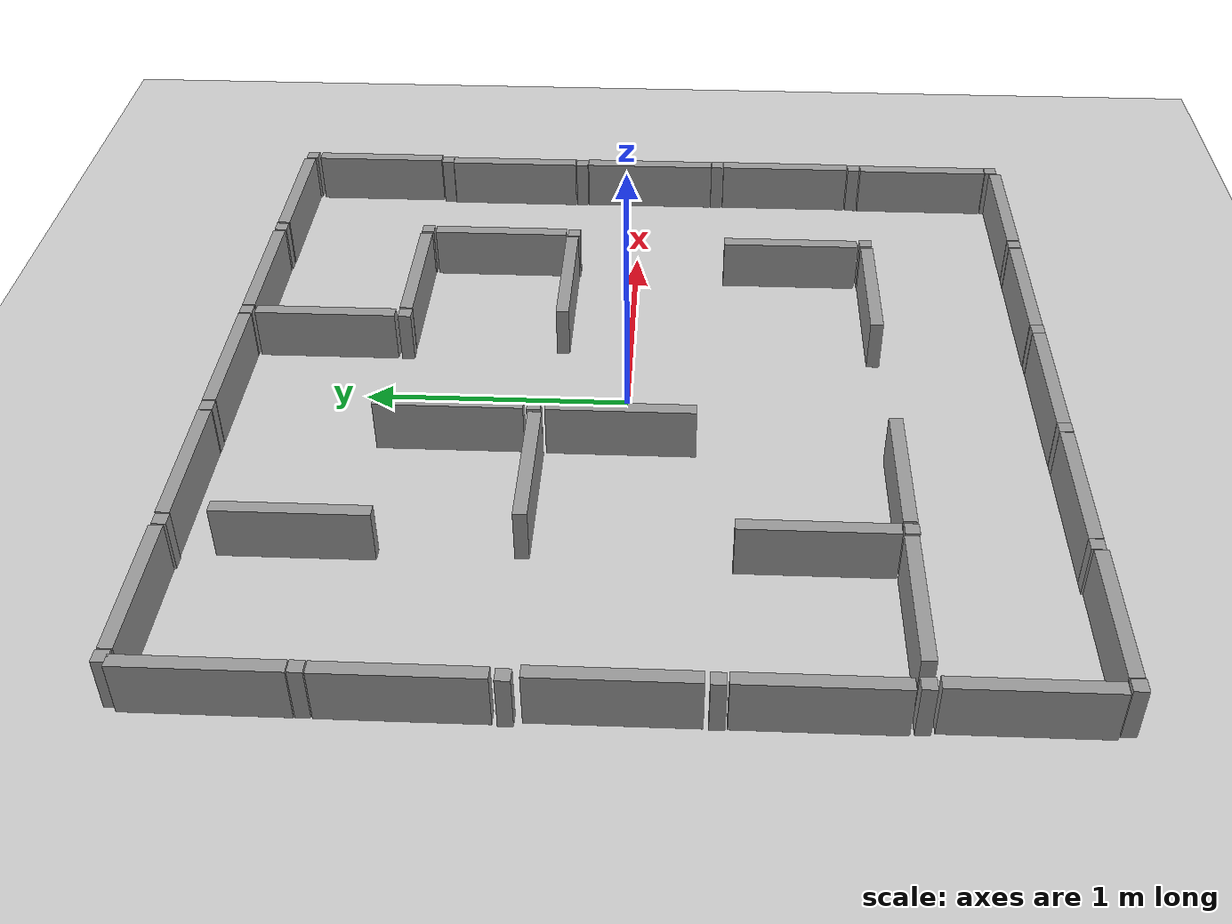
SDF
<?xml version="1.0" ?>

<sdf version="1.5">
	<world name="default">
		<!-- A global light source -->
		<include>
			<uri>model://sun</uri>
		</include>

		<!-- A ground plane -->
		<include>
			<uri>model://ground_plane</uri>
		</include>

		<include>
			<uri>model://white_maze</uri>
		</include>

	</world>
</sdf>

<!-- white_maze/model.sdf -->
<sdf version='1.6'>
  <model name='white_maze'>
    <link name='link_0'>
      <inertial>
        <mass>1</mass>
        <inertia>
          <ixx>0.166667</ixx>
          <ixy>0</ixy>
          <ixz>0</ixz>
          <iyy>0.166667</iyy>
          <iyz>0</iyz>
          <izz>0.166667</izz>
        </inertia>
        <pose frame=''>0 0 0 0 -0 0</pose>
      </inertial>
      <pose frame=''>-1.23382 -1.58127 0 0 -0 0</pose>
      <gravity>1</gravity>
      <self_collide>0</self_collide>
      <kinematic>0</kinematic>
      <enable_wind>0</enable_wind>
      <visual name='visual'>
        <pose frame=''>0 0 0 0 -0 0</pose>
        <geometry>
          <box>
            <size>0.55 0.05 0.4</size>
          </box>
        </geometry>
        <material>
          <lighting>1</lighting>
          <script>
            <uri>file://media/materials/scripts/gazebo.material</uri>
            <name>Gazebo/Grey</name>
          </script>
          <shader type='vertex'>
            <normal_map>__default__</normal_map>
          </shader>
          <ambient>1 1 1 1</ambient>
          <diffuse>0.7 0.7 0.7 1</diffuse>
          <specular>0.01 0.01 0.01 1</specular>
          <emissive>0 0 0 1</emissive>
        </material>
        <transparency>0</transparency>
        <cast_shadows>1</cast_shadows>
      </visual>
      <collision name='collision'>
        <laser_retro>0</laser_retro>
        <max_contacts>10</max_contacts>
        <pose frame=''>0 0 0 0 -0 0</pose>
        <geometry>
          <box>
            <size>0.55 0.05 0.4</size>
          </box>
        </geometry>
        <surface>
          <friction>
            <ode>
              <mu>1</mu>
              <mu2>1</mu2>
              <fdir1>0 0 0</fdir1>
              <slip1>0</slip1>
              <slip2>0</slip2>
            </ode>
            <torsional>
              <coefficient>1</coefficient>
              <patch_radius>0</patch_radius>
              <surface_radius>0</surface_radius>
              <use_patch_radius>1</use_patch_radius>
              <ode>
                <slip>0</slip>
              </ode>
            </torsional>
          </friction>
          <bounce>
            <restitution_coefficient>0</restitution_coefficient>
            <threshold>1e+06</threshold>
          </bounce>
          <contact>
            <collide_without_contact>0</collide_without_contact>
            <collide_without_contact_bitmask>1</collide_without_contact_bitmask>
            <collide_bitmask>1</collide_bitmask>
            <ode>
              <soft_cfm>0</soft_cfm>
              <soft_erp>0.2</soft_erp>
              <kp>1e+13</kp>
              <kd>1</kd>
              <max_vel>0.01</max_vel>
              <min_depth>0</min_depth>
            </ode>
            <bullet>
              <split_impulse>1</split_impulse>
              <split_impulse_penetration_threshold>-0.01</split_impulse_penetration_threshold>
              <soft_cfm>0</soft_cfm>
              <soft_erp>0.2</soft_erp>
              <kp>1e+13</kp>
              <kd>1</kd>
            </bullet>
          </contact>
        </surface>
      </collision>
    </link>
    <link name='link_0_clone'>
      <inertial>
        <mass>1</mass>
        <inertia>
          <ixx>0.166667</ixx>
          <ixy>0</ixy>
          <ixz>0</ixz>
          <iyy>0.166667</iyy>
          <iyz>0</iyz>
          <izz>0.166667</izz>
        </inertia>
        <pose frame=''>0 0 0 0 -0 0</pose>
      </inertial>
      <pose frame=''>-0.627493 -1.57445 0 0 -0 0</pose>
      <gravity>1</gravity>
      <self_collide>0</self_collide>
      <kinematic>0</kinematic>
      <enable_wind>0</enable_wind>
      <visual name='visual'>
        <pose frame=''>0 0 0 0 -0 0</pose>
        <geometry>
          <box>
            <size>0.55 0.05 0.4</size>
          </box>
        </geometry>
        <material>
          <lighting>1</lighting>
          <script>
            <uri>file://media/materials/scripts/gazebo.material</uri>
            <name>Gazebo/Grey</name>
          </script>
          <shader type='vertex'>
            <normal_map>__default__</normal_map>
          </shader>
          <ambient>1 1 1 1</ambient>
          <diffuse>0.7 0.7 0.7 1</diffuse>
          <specular>0.01 0.01 0.01 1</specular>
          <emissive>0 0 0 1</emissive>
        </material>
        <transparency>0</transparency>
        <cast_shadows>1</cast_shadows>
      </visual>
      <collision name='collision'>
        <laser_retro>0</laser_retro>
        <max_contacts>10</max_contacts>
        <pose frame=''>0 0 0 0 -0 0</pose>
        <geometry>
          <box>
            <size>0.55 0.05 0.4</size>
          </box>
        </geometry>
        <surface>
          <friction>
            <ode>
              <mu>1</mu>
              <mu2>1</mu2>
              <fdir1>0 0 0</fdir1>
              <slip1>0</slip1>
              <slip2>0</slip2>
            </ode>
            <torsional>
              <coefficient>1</coefficient>
              <patch_radius>0</patch_radius>
              <surface_radius>0</surface_radius>
              <use_patch_radius>1</use_patch_radius>
              <ode>
                <slip>0</slip>
              </ode>
            </torsional>
          </friction>
          <bounce>
            <restitution_coefficient>0</restitution_coefficient>
            <threshold>1e+06</threshold>
          </bounce>
          <contact>
            <collide_without_contact>0</collide_without_contact>
            <collide_without_contact_bitmask>1</collide_without_contact_bitmask>
            <collide_bitmask>1</collide_bitmask>
            <ode>
              <soft_cfm>0</soft_cfm>
              <soft_erp>0.2</soft_erp>
              <kp>1e+13</kp>
              <kd>1</kd>
              <max_vel>0.01</max_vel>
              <min_depth>0</min_depth>
            </ode>
            <bullet>
              <split_impulse>1</split_impulse>
              <split_impulse_penetration_threshold>-0.01</split_impulse_penetration_threshold>
              <soft_cfm>0</soft_cfm>
              <soft_erp>0.2</soft_erp>
              <kp>1e+13</kp>
              <kd>1</kd>
            </bullet>
          </contact>
        </surface>
      </collision>
    </link>
    <link name='link_0_clone_0'>
      <inertial>
        <mass>1</mass>
        <inertia>
          <ixx>0.166667</ixx>
          <ixy>0</ixy>
          <ixz>0</ixz>
          <iyy>0.166667</iyy>
          <iyz>0</iyz>
          <izz>0.166667</izz>
        </inertia>
        <pose frame=''>0 0 0 0 -0 0</pose>
      </inertial>
      <pose frame=''>-0.023747 -1.57344 0 0 -0 0</pose>
      <gravity>1</gravity>
      <self_collide>0</self_collide>
      <kinematic>0</kinematic>
      <enable_wind>0</enable_wind>
      <visual name='visual'>
        <pose frame=''>0 0 0 0 -0 0</pose>
        <geometry>
          <box>
            <size>0.55 0.05 0.4</size>
          </box>
        </geometry>
        <material>
          <lighting>1</lighting>
          <script>
            <uri>file://media/materials/scripts/gazebo.material</uri>
            <name>Gazebo/Grey</name>
          </script>
          <shader type='vertex'>
            <normal_map>__default__</normal_map>
          </shader>
          <ambient>1 1 1 1</ambient>
          <diffuse>0.7 0.7 0.7 1</diffuse>
          <specular>0.01 0.01 0.01 1</specular>
          <emissive>0 0 0 1</emissive>
        </material>
        <transparency>0</transparency>
        <cast_shadows>1</cast_shadows>
      </visual>
      <collision name='collision'>
        <laser_retro>0</laser_retro>
        <max_contacts>10</max_contacts>
        <pose frame=''>0 0 0 0 -0 0</pose>
        <geometry>
          <box>
            <size>0.55 0.05 0.4</size>
          </box>
        </geometry>
        <surface>
          <friction>
            <ode>
              <mu>1</mu>
              <mu2>1</mu2>
              <fdir1>0 0 0</fdir1>
              <slip1>0</slip1>
              <slip2>0</slip2>
            </ode>
            <torsional>
              <coefficient>1</coefficient>
              <patch_radius>0</patch_radius>
              <surface_radius>0</surface_radius>
              <use_patch_radius>1</use_patch_radius>
              <ode>
                <slip>0</slip>
              </ode>
            </torsional>
          </friction>
          <bounce>
            <restitution_coefficient>0</restitution_coefficient>
            <threshold>1e+06</threshold>
          </bounce>
          <contact>
            <collide_without_contact>0</collide_without_contact>
            <collide_without_contact_bitmask>1</collide_without_contact_bitmask>
            <collide_bitmask>1</collide_bitmask>
            <ode>
              <soft_cfm>0</soft_cfm>
              <soft_erp>0.2</soft_erp>
              <kp>1e+13</kp>
              <kd>1</kd>
              <max_vel>0.01</max_vel>
              <min_depth>0</min_depth>
            </ode>
            <bullet>
              <split_impulse>1</split_impulse>
              <split_impulse_penetration_threshold>-0.01</split_impulse_penetration_threshold>
              <soft_cfm>0</soft_cfm>
              <soft_erp>0.2</soft_erp>
              <kp>1e+13</kp>
              <kd>1</kd>
            </bullet>
          </contact>
        </surface>
      </collision>
    </link>
    <link name='link_0_clone_1'>
      <inertial>
        <mass>1</mass>
        <inertia>
          <ixx>0.166667</ixx>
          <ixy>0</ixy>
          <ixz>0</ixz>
          <iyy>0.166667</iyy>
          <iyz>0</iyz>
          <izz>0.166667</izz>
        </inertia>
        <pose frame=''>0 0 0 0 -0 0</pose>
      </inertial>
      <pose frame=''>0.582587 -1.57153 0 0 -0 0</pose>
      <gravity>1</gravity>
      <self_collide>0</self_collide>
      <kinematic>0</kinematic>
      <enable_wind>0</enable_wind>
      <visual name='visual'>
        <pose frame=''>0 0 0 0 -0 0</pose>
        <geometry>
          <box>
            <size>0.55 0.05 0.4</size>
          </box>
        </geometry>
        <material>
          <lighting>1</lighting>
          <script>
            <uri>file://media/materials/scripts/gazebo.material</uri>
            <name>Gazebo/Grey</name>
          </script>
          <shader type='vertex'>
            <normal_map>__default__</normal_map>
          </shader>
          <ambient>1 1 1 1</ambient>
          <diffuse>0.7 0.7 0.7 1</diffuse>
          <specular>0.01 0.01 0.01 1</specular>
          <emissive>0 0 0 1</emissive>
        </material>
        <transparency>0</transparency>
        <cast_shadows>1</cast_shadows>
      </visual>
      <collision name='collision'>
        <laser_retro>0</laser_retro>
        <max_contacts>10</max_contacts>
        <pose frame=''>0 0 0 0 -0 0</pose>
        <geometry>
          <box>
            <size>0.55 0.05 0.4</size>
          </box>
        </geometry>
        <surface>
          <friction>
            <ode>
              <mu>1</mu>
              <mu2>1</mu2>
              <fdir1>0 0 0</fdir1>
              <slip1>0</slip1>
              <slip2>0</slip2>
            </ode>
            <torsional>
              <coefficient>1</coefficient>
              <patch_radius>0</patch_radius>
              <surface_radius>0</surface_radius>
              <use_patch_radius>1</use_patch_radius>
              <ode>
                <slip>0</slip>
              </ode>
            </torsional>
          </friction>
          <bounce>
            <restitution_coefficient>0</restitution_coefficient>
            <threshold>1e+06</threshold>
          </bounce>
          <contact>
            <collide_without_contact>0</collide_without_contact>
            <collide_without_contact_bitmask>1</collide_without_contact_bitmask>
            <collide_bitmask>1</collide_bitmask>
            <ode>
              <soft_cfm>0</soft_cfm>
              <soft_erp>0.2</soft_erp>
              <kp>1e+13</kp>
              <kd>1</kd>
              <max_vel>0.01</max_vel>
              <min_depth>0</min_depth>
            </ode>
            <bullet>
              <split_impulse>1</split_impulse>
              <split_impulse_penetration_threshold>-0.01</split_impulse_penetration_threshold>
              <soft_cfm>0</soft_cfm>
              <soft_erp>0.2</soft_erp>
              <kp>1e+13</kp>
              <kd>1</kd>
            </bullet>
          </contact>
        </surface>
      </collision>
    </link>
    <link name='link_0_clone_1_clone'>
      <inertial>
        <mass>1</mass>
        <inertia>
          <ixx>0.166667</ixx>
          <ixy>0</ixy>
          <ixz>0</ixz>
          <iyy>0.166667</iyy>
          <iyz>0</iyz>
          <izz>0.166667</izz>
        </inertia>
        <pose frame=''>0 0 0 0 -0 0</pose>
      </inertial>
      <pose frame=''>1.49724 -1.25172 0 0 0 -1.57264</pose>
      <gravity>1</gravity>
      <self_collide>0</self_collide>
      <kinematic>0</kinematic>
      <enable_wind>0</enable_wind>
      <visual name='visual'>
        <pose frame=''>0 0 0 0 -0 0</pose>
        <geometry>
          <box>
            <size>0.55 0.05 0.4</size>
          </box>
        </geometry>
        <material>
          <lighting>1</lighting>
          <script>
            <uri>file://media/materials/scripts/gazebo.material</uri>
            <name>Gazebo/Grey</name>
          </script>
          <shader type='vertex'>
            <normal_map>__default__</normal_map>
          </shader>
          <ambient>1 1 1 1</ambient>
          <diffuse>0.7 0.7 0.7 1</diffuse>
          <specular>0.01 0.01 0.01 1</specular>
          <emissive>0 0 0 1</emissive>
        </material>
        <transparency>0</transparency>
        <cast_shadows>1</cast_shadows>
      </visual>
      <collision name='collision'>
        <laser_retro>0</laser_retro>
        <max_contacts>10</max_contacts>
        <pose frame=''>0 0 0 0 -0 0</pose>
        <geometry>
          <box>
            <size>0.55 0.05 0.4</size>
          </box>
        </geometry>
        <surface>
          <friction>
            <ode>
              <mu>1</mu>
              <mu2>1</mu2>
              <fdir1>0 0 0</fdir1>
              <slip1>0</slip1>
              <slip2>0</slip2>
            </ode>
            <torsional>
              <coefficient>1</coefficient>
              <patch_radius>0</patch_radius>
              <surface_radius>0</surface_radius>
              <use_patch_radius>1</use_patch_radius>
              <ode>
                <slip>0</slip>
              </ode>
            </torsional>
          </friction>
          <bounce>
            <restitution_coefficient>0</restitution_coefficient>
            <threshold>1e+06</threshold>
          </bounce>
          <contact>
            <collide_without_contact>0</collide_without_contact>
            <collide_without_contact_bitmask>1</collide_without_contact_bitmask>
            <collide_bitmask>1</collide_bitmask>
            <ode>
              <soft_cfm>0</soft_cfm>
              <soft_erp>0.2</soft_erp>
              <kp>1e+13</kp>
              <kd>1</kd>
              <max_vel>0.01</max_vel>
              <min_depth>0</min_depth>
            </ode>
            <bullet>
              <split_impulse>1</split_impulse>
              <split_impulse_penetration_threshold>-0.01</split_impulse_penetration_threshold>
              <soft_cfm>0</soft_cfm>
              <soft_erp>0.2</soft_erp>
              <kp>1e+13</kp>
              <kd>1</kd>
            </bullet>
          </contact>
        </surface>
      </collision>
    </link>
    <link name='link_0_clone_1_clone_0'>
      <inertial>
        <mass>1</mass>
        <inertia>
          <ixx>0.166667</ixx>
          <ixy>0</ixy>
          <ixz>0</ixz>
          <iyy>0.166667</iyy>
          <iyz>0</iyz>
          <izz>0.166667</izz>
        </inertia>
        <pose frame=''>0 0 0 0 -0 0</pose>
      </inertial>
      <pose frame=''>1.21099 1.50565 0 0 -0 0</pose>
      <gravity>1</gravity>
      <self_collide>0</self_collide>
      <kinematic>0</kinematic>
      <enable_wind>0</enable_wind>
      <visual name='visual'>
        <pose frame=''>0 0 0 0 -0 0</pose>
        <geometry>
          <box>
            <size>0.55 0.05 0.4</size>
          </box>
        </geometry>
        <material>
          <lighting>1</lighting>
          <script>
            <uri>file://media/materials/scripts/gazebo.material</uri>
            <name>Gazebo/Grey</name>
          </script>
          <shader type='vertex'>
            <normal_map>__default__</normal_map>
          </shader>
          <ambient>1 1 1 1</ambient>
          <diffuse>0.7 0.7 0.7 1</diffuse>
          <specular>0.01 0.01 0.01 1</specular>
          <emissive>0 0 0 1</emissive>
        </material>
        <transparency>0</transparency>
        <cast_shadows>1</cast_shadows>
      </visual>
      <collision name='collision'>
        <laser_retro>0</laser_retro>
        <max_contacts>10</max_contacts>
        <pose frame=''>0 0 0 0 -0 0</pose>
        <geometry>
          <box>
            <size>0.55 0.05 0.4</size>
          </box>
        </geometry>
        <surface>
          <friction>
            <ode>
              <mu>1</mu>
              <mu2>1</mu2>
              <fdir1>0 0 0</fdir1>
              <slip1>0</slip1>
              <slip2>0</slip2>
            </ode>
            <torsional>
              <coefficient>1</coefficient>
              <patch_radius>0</patch_radius>
              <surface_radius>0</surface_radius>
              <use_patch_radius>1</use_patch_radius>
              <ode>
                <slip>0</slip>
              </ode>
            </torsional>
          </friction>
          <bounce>
            <restitution_coefficient>0</restitution_coefficient>
            <threshold>1e+06</threshold>
          </bounce>
          <contact>
            <collide_without_contact>0</collide_without_contact>
            <collide_without_contact_bitmask>1</collide_without_contact_bitmask>
            <collide_bitmask>1</collide_bitmask>
            <ode>
              <soft_cfm>0</soft_cfm>
              <soft_erp>0.2</soft_erp>
              <kp>1e+13</kp>
              <kd>1</kd>
              <max_vel>0.01</max_vel>
              <min_depth>0</min_depth>
            </ode>
            <bullet>
              <split_impulse>1</split_impulse>
              <split_impulse_penetration_threshold>-0.01</split_impulse_penetration_threshold>
              <soft_cfm>0</soft_cfm>
              <soft_erp>0.2</soft_erp>
              <kp>1e+13</kp>
              <kd>1</kd>
            </bullet>
          </contact>
        </surface>
      </collision>
    </link>
    <link name='link_0_clone_1_clone_1'>
      <inertial>
        <mass>1</mass>
        <inertia>
          <ixx>0.166667</ixx>
          <ixy>0</ixy>
          <ixz>0</ixz>
          <iyy>0.166667</iyy>
          <iyz>0</iyz>
          <izz>0.166667</izz>
        </inertia>
        <pose frame=''>0 0 0 0 -0 0</pose>
      </inertial>
      <pose frame=''>0.593667 1.50999 0 0 -0 0</pose>
      <gravity>1</gravity>
      <self_collide>0</self_collide>
      <kinematic>0</kinematic>
      <enable_wind>0</enable_wind>
      <visual name='visual'>
        <pose frame=''>0 0 0 0 -0 0</pose>
        <geometry>
          <box>
            <size>0.55 0.05 0.4</size>
          </box>
        </geometry>
        <material>
          <lighting>1</lighting>
          <script>
            <uri>file://media/materials/scripts/gazebo.material</uri>
            <name>Gazebo/Grey</name>
          </script>
          <shader type='vertex'>
            <normal_map>__default__</normal_map>
          </shader>
          <ambient>1 1 1 1</ambient>
          <diffuse>0.7 0.7 0.7 1</diffuse>
          <specular>0.01 0.01 0.01 1</specular>
          <emissive>0 0 0 1</emissive>
        </material>
        <transparency>0</transparency>
        <cast_shadows>1</cast_shadows>
      </visual>
      <collision name='collision'>
        <laser_retro>0</laser_retro>
        <max_contacts>10</max_contacts>
        <pose frame=''>0 0 0 0 -0 0</pose>
        <geometry>
          <box>
            <size>0.55 0.05 0.4</size>
          </box>
        </geometry>
        <surface>
          <friction>
            <ode>
              <mu>1</mu>
              <mu2>1</mu2>
              <fdir1>0 0 0</fdir1>
              <slip1>0</slip1>
              <slip2>0</slip2>
            </ode>
            <torsional>
              <coefficient>1</coefficient>
              <patch_radius>0</patch_radius>
              <surface_radius>0</surface_radius>
              <use_patch_radius>1</use_patch_radius>
              <ode>
                <slip>0</slip>
              </ode>
            </torsional>
          </friction>
          <bounce>
            <restitution_coefficient>0</restitution_coefficient>
            <threshold>1e+06</threshold>
          </bounce>
          <contact>
            <collide_without_contact>0</collide_without_contact>
            <collide_without_contact_bitmask>1</collide_without_contact_bitmask>
            <collide_bitmask>1</collide_bitmask>
            <ode>
              <soft_cfm>0</soft_cfm>
              <soft_erp>0.2</soft_erp>
              <kp>1e+13</kp>
              <kd>1</kd>
              <max_vel>0.01</max_vel>
              <min_depth>0</min_depth>
            </ode>
            <bullet>
              <split_impulse>1</split_impulse>
              <split_impulse_penetration_threshold>-0.01</split_impulse_penetration_threshold>
              <soft_cfm>0</soft_cfm>
              <soft_erp>0.2</soft_erp>
              <kp>1e+13</kp>
              <kd>1</kd>
            </bullet>
          </contact>
        </surface>
      </collision>
    </link>
    <link name='link_0_clone_1_clone_2'>
      <inertial>
        <mass>1</mass>
        <inertia>
          <ixx>0.166667</ixx>
          <ixy>0</ixy>
          <ixz>0</ixz>
          <iyy>0.166667</iyy>
          <iyz>0</iyz>
          <izz>0.166667</izz>
        </inertia>
        <pose frame=''>0 0 0 0 -0 0</pose>
      </inertial>
      <pose frame=''>-0.019419 1.51088 0 0 -0 0</pose>
      <gravity>1</gravity>
      <self_collide>0</self_collide>
      <kinematic>0</kinematic>
      <enable_wind>0</enable_wind>
      <visual name='visual'>
        <pose frame=''>0 0 0 0 -0 0</pose>
        <geometry>
          <box>
            <size>0.55 0.05 0.4</size>
          </box>
        </geometry>
        <material>
          <lighting>1</lighting>
          <script>
            <uri>file://media/materials/scripts/gazebo.material</uri>
            <name>Gazebo/Grey</name>
          </script>
          <shader type='vertex'>
            <normal_map>__default__</normal_map>
          </shader>
          <ambient>1 1 1 1</ambient>
          <diffuse>0.7 0.7 0.7 1</diffuse>
          <specular>0.01 0.01 0.01 1</specular>
          <emissive>0 0 0 1</emissive>
        </material>
        <transparency>0</transparency>
        <cast_shadows>1</cast_shadows>
      </visual>
      <collision name='collision'>
        <laser_retro>0</laser_retro>
        <max_contacts>10</max_contacts>
        <pose frame=''>0 0 0 0 -0 0</pose>
        <geometry>
          <box>
            <size>0.55 0.05 0.4</size>
          </box>
        </geometry>
        <surface>
          <friction>
            <ode>
              <mu>1</mu>
              <mu2>1</mu2>
              <fdir1>0 0 0</fdir1>
              <slip1>0</slip1>
              <slip2>0</slip2>
            </ode>
            <torsional>
              <coefficient>1</coefficient>
              <patch_radius>0</patch_radius>
              <surface_radius>0</surface_radius>
              <use_patch_radius>1</use_patch_radius>
              <ode>
                <slip>0</slip>
              </ode>
            </torsional>
          </friction>
          <bounce>
            <restitution_coefficient>0</restitution_coefficient>
            <threshold>1e+06</threshold>
          </bounce>
          <contact>
            <collide_without_contact>0</collide_without_contact>
            <collide_without_contact_bitmask>1</collide_without_contact_bitmask>
            <collide_bitmask>1</collide_bitmask>
            <ode>
              <soft_cfm>0</soft_cfm>
              <soft_erp>0.2</soft_erp>
              <kp>1e+13</kp>
              <kd>1</kd>
              <max_vel>0.01</max_vel>
              <min_depth>0</min_depth>
            </ode>
            <bullet>
              <split_impulse>1</split_impulse>
              <split_impulse_penetration_threshold>-0.01</split_impulse_penetration_threshold>
              <soft_cfm>0</soft_cfm>
              <soft_erp>0.2</soft_erp>
              <kp>1e+13</kp>
              <kd>1</kd>
            </bullet>
          </contact>
        </surface>
      </collision>
    </link>
    <link name='link_0_clone_1_clone_3'>
      <inertial>
        <mass>1</mass>
        <inertia>
          <ixx>0.166667</ixx>
          <ixy>0</ixy>
          <ixz>0</ixz>
          <iyy>0.166667</iyy>
          <iyz>0</iyz>
          <izz>0.166667</izz>
        </inertia>
        <pose frame=''>0 0 0 0 -0 0</pose>
      </inertial>
      <pose frame=''>-0.630178 1.51122 0 0 -0 0</pose>
      <gravity>1</gravity>
      <self_collide>0</self_collide>
      <kinematic>0</kinematic>
      <enable_wind>0</enable_wind>
      <visual name='visual'>
        <pose frame=''>0 0 0 0 -0 0</pose>
        <geometry>
          <box>
            <size>0.55 0.05 0.4</size>
          </box>
        </geometry>
        <material>
          <lighting>1</lighting>
          <script>
            <uri>file://media/materials/scripts/gazebo.material</uri>
            <name>Gazebo/Grey</name>
          </script>
          <shader type='vertex'>
            <normal_map>__default__</normal_map>
          </shader>
          <ambient>1 1 1 1</ambient>
          <diffuse>0.7 0.7 0.7 1</diffuse>
          <specular>0.01 0.01 0.01 1</specular>
          <emissive>0 0 0 1</emissive>
        </material>
        <transparency>0</transparency>
        <cast_shadows>1</cast_shadows>
      </visual>
      <collision name='collision'>
        <laser_retro>0</laser_retro>
        <max_contacts>10</max_contacts>
        <pose frame=''>0 0 0 0 -0 0</pose>
        <geometry>
          <box>
            <size>0.55 0.05 0.4</size>
          </box>
        </geometry>
        <surface>
          <friction>
            <ode>
              <mu>1</mu>
              <mu2>1</mu2>
              <fdir1>0 0 0</fdir1>
              <slip1>0</slip1>
              <slip2>0</slip2>
            </ode>
            <torsional>
              <coefficient>1</coefficient>
              <patch_radius>0</patch_radius>
              <surface_radius>0</surface_radius>
              <use_patch_radius>1</use_patch_radius>
              <ode>
                <slip>0</slip>
              </ode>
            </torsional>
          </friction>
          <bounce>
            <restitution_coefficient>0</restitution_coefficient>
            <threshold>1e+06</threshold>
          </bounce>
          <contact>
            <collide_without_contact>0</collide_without_contact>
            <collide_without_contact_bitmask>1</collide_without_contact_bitmask>
            <collide_bitmask>1</collide_bitmask>
            <ode>
              <soft_cfm>0</soft_cfm>
              <soft_erp>0.2</soft_erp>
              <kp>1e+13</kp>
              <kd>1</kd>
              <max_vel>0.01</max_vel>
              <min_depth>0</min_depth>
            </ode>
            <bullet>
              <split_impulse>1</split_impulse>
              <split_impulse_penetration_threshold>-0.01</split_impulse_penetration_threshold>
              <soft_cfm>0</soft_cfm>
              <soft_erp>0.2</soft_erp>
              <kp>1e+13</kp>
              <kd>1</kd>
            </bullet>
          </contact>
        </surface>
      </collision>
    </link>
    <link name='link_0_clone_1_clone_4'>
      <inertial>
        <mass>1</mass>
        <inertia>
          <ixx>0.166667</ixx>
          <ixy>0</ixy>
          <ixz>0</ixz>
          <iyy>0.166667</iyy>
          <iyz>0</iyz>
          <izz>0.166667</izz>
        </inertia>
        <pose frame=''>0 0 0 0 -0 0</pose>
      </inertial>
      <pose frame=''>-1.24431 1.51418 0 0 -0 0</pose>
      <gravity>1</gravity>
      <self_collide>0</self_collide>
      <kinematic>0</kinematic>
      <enable_wind>0</enable_wind>
      <visual name='visual'>
        <pose frame=''>0 0 0 0 -0 0</pose>
        <geometry>
          <box>
            <size>0.55 0.05 0.4</size>
          </box>
        </geometry>
        <material>
          <lighting>1</lighting>
          <script>
            <uri>file://media/materials/scripts/gazebo.material</uri>
            <name>Gazebo/Grey</name>
          </script>
          <shader type='vertex'>
            <normal_map>__default__</normal_map>
          </shader>
          <ambient>1 1 1 1</ambient>
          <diffuse>0.7 0.7 0.7 1</diffuse>
          <specular>0.01 0.01 0.01 1</specular>
          <emissive>0 0 0 1</emissive>
        </material>
        <transparency>0</transparency>
        <cast_shadows>1</cast_shadows>
      </visual>
      <collision name='collision'>
        <laser_retro>0</laser_retro>
        <max_contacts>10</max_contacts>
        <pose frame=''>0 0 0 0 -0 0</pose>
        <geometry>
          <box>
            <size>0.55 0.05 0.4</size>
          </box>
        </geometry>
        <surface>
          <friction>
            <ode>
              <mu>1</mu>
              <mu2>1</mu2>
              <fdir1>0 0 0</fdir1>
              <slip1>0</slip1>
              <slip2>0</slip2>
            </ode>
            <torsional>
              <coefficient>1</coefficient>
              <patch_radius>0</patch_radius>
              <surface_radius>0</surface_radius>
              <use_patch_radius>1</use_patch_radius>
              <ode>
                <slip>0</slip>
              </ode>
            </torsional>
          </friction>
          <bounce>
            <restitution_coefficient>0</restitution_coefficient>
            <threshold>1e+06</threshold>
          </bounce>
          <contact>
            <collide_without_contact>0</collide_without_contact>
            <collide_without_contact_bitmask>1</collide_without_contact_bitmask>
            <collide_bitmask>1</collide_bitmask>
            <ode>
              <soft_cfm>0</soft_cfm>
              <soft_erp>0.2</soft_erp>
              <kp>1e+13</kp>
              <kd>1</kd>
              <max_vel>0.01</max_vel>
              <min_depth>0</min_depth>
            </ode>
            <bullet>
              <split_impulse>1</split_impulse>
              <split_impulse_penetration_threshold>-0.01</split_impulse_penetration_threshold>
              <soft_cfm>0</soft_cfm>
              <soft_erp>0.2</soft_erp>
              <kp>1e+13</kp>
              <kd>1</kd>
            </bullet>
          </contact>
        </surface>
      </collision>
    </link>
    <link name='link_0_clone_1_clone_clone'>
      <inertial>
        <mass>1</mass>
        <inertia>
          <ixx>0.166667</ixx>
          <ixy>0</ixy>
          <ixz>0</ixz>
          <iyy>0.166667</iyy>
          <iyz>0</iyz>
          <izz>0.166667</izz>
        </inertia>
        <pose frame=''>0 0 0 0 -0 0</pose>
      </inertial>
      <pose frame=''>1.504 -0.640018 0 0 0 -1.57264</pose>
      <gravity>1</gravity>
      <self_collide>0</self_collide>
      <kinematic>0</kinematic>
      <enable_wind>0</enable_wind>
      <visual name='visual'>
        <pose frame=''>0 0 0 0 -0 0</pose>
        <geometry>
          <box>
            <size>0.55 0.05 0.4</size>
          </box>
        </geometry>
        <material>
          <lighting>1</lighting>
          <script>
            <uri>file://media/materials/scripts/gazebo.material</uri>
            <name>Gazebo/Grey</name>
          </script>
          <shader type='vertex'>
            <normal_map>__default__</normal_map>
          </shader>
          <ambient>1 1 1 1</ambient>
          <diffuse>0.7 0.7 0.7 1</diffuse>
          <specular>0.01 0.01 0.01 1</specular>
          <emissive>0 0 0 1</emissive>
        </material>
        <transparency>0</transparency>
        <cast_shadows>1</cast_shadows>
      </visual>
      <collision name='collision'>
        <laser_retro>0</laser_retro>
        <max_contacts>10</max_contacts>
        <pose frame=''>0 0 0 0 -0 0</pose>
        <geometry>
          <box>
            <size>0.55 0.05 0.4</size>
          </box>
        </geometry>
        <surface>
          <friction>
            <ode>
              <mu>1</mu>
              <mu2>1</mu2>
              <fdir1>0 0 0</fdir1>
              <slip1>0</slip1>
              <slip2>0</slip2>
            </ode>
            <torsional>
              <coefficient>1</coefficient>
              <patch_radius>0</patch_radius>
              <surface_radius>0</surface_radius>
              <use_patch_radius>1</use_patch_radius>
              <ode>
                <slip>0</slip>
              </ode>
            </torsional>
          </friction>
          <bounce>
            <restitution_coefficient>0</restitution_coefficient>
            <threshold>1e+06</threshold>
          </bounce>
          <contact>
            <collide_without_contact>0</collide_without_contact>
            <collide_without_contact_bitmask>1</collide_without_contact_bitmask>
            <collide_bitmask>1</collide_bitmask>
            <ode>
              <soft_cfm>0</soft_cfm>
              <soft_erp>0.2</soft_erp>
              <kp>1e+13</kp>
              <kd>1</kd>
              <max_vel>0.01</max_vel>
              <min_depth>0</min_depth>
            </ode>
            <bullet>
              <split_impulse>1</split_impulse>
              <split_impulse_penetration_threshold>-0.01</split_impulse_penetration_threshold>
              <soft_cfm>0</soft_cfm>
              <soft_erp>0.2</soft_erp>
              <kp>1e+13</kp>
              <kd>1</kd>
            </bullet>
          </contact>
        </surface>
      </collision>
    </link>
    <link name='link_0_clone_1_clone_clone_0'>
      <inertial>
        <mass>1</mass>
        <inertia>
          <ixx>0.166667</ixx>
          <ixy>0</ixy>
          <ixz>0</ixz>
          <iyy>0.166667</iyy>
          <iyz>0</iyz>
          <izz>0.166667</izz>
        </inertia>
        <pose frame=''>0 0 0 0 -0 0</pose>
      </inertial>
      <pose frame=''>1.50232 -0.033133 0 0 0 -1.57264</pose>
      <gravity>1</gravity>
      <self_collide>0</self_collide>
      <kinematic>0</kinematic>
      <enable_wind>0</enable_wind>
      <visual name='visual'>
        <pose frame=''>0 0 0 0 -0 0</pose>
        <geometry>
          <box>
            <size>0.55 0.05 0.4</size>
          </box>
        </geometry>
        <material>
          <lighting>1</lighting>
          <script>
            <uri>file://media/materials/scripts/gazebo.material</uri>
            <name>Gazebo/Grey</name>
          </script>
          <shader type='vertex'>
            <normal_map>__default__</normal_map>
          </shader>
          <ambient>1 1 1 1</ambient>
          <diffuse>0.7 0.7 0.7 1</diffuse>
          <specular>0.01 0.01 0.01 1</specular>
          <emissive>0 0 0 1</emissive>
        </material>
        <transparency>0</transparency>
        <cast_shadows>1</cast_shadows>
      </visual>
      <collision name='collision'>
        <laser_retro>0</laser_retro>
        <max_contacts>10</max_contacts>
        <pose frame=''>0 0 0 0 -0 0</pose>
        <geometry>
          <box>
            <size>0.55 0.05 0.4</size>
          </box>
        </geometry>
        <surface>
          <friction>
            <ode>
              <mu>1</mu>
              <mu2>1</mu2>
              <fdir1>0 0 0</fdir1>
              <slip1>0</slip1>
              <slip2>0</slip2>
            </ode>
            <torsional>
              <coefficient>1</coefficient>
              <patch_radius>0</patch_radius>
              <surface_radius>0</surface_radius>
              <use_patch_radius>1</use_patch_radius>
              <ode>
                <slip>0</slip>
              </ode>
            </torsional>
          </friction>
          <bounce>
            <restitution_coefficient>0</restitution_coefficient>
            <threshold>1e+06</threshold>
          </bounce>
          <contact>
            <collide_without_contact>0</collide_without_contact>
            <collide_without_contact_bitmask>1</collide_without_contact_bitmask>
            <collide_bitmask>1</collide_bitmask>
            <ode>
              <soft_cfm>0</soft_cfm>
              <soft_erp>0.2</soft_erp>
              <kp>1e+13</kp>
              <kd>1</kd>
              <max_vel>0.01</max_vel>
              <min_depth>0</min_depth>
            </ode>
            <bullet>
              <split_impulse>1</split_impulse>
              <split_impulse_penetration_threshold>-0.01</split_impulse_penetration_threshold>
              <soft_cfm>0</soft_cfm>
              <soft_erp>0.2</soft_erp>
              <kp>1e+13</kp>
              <kd>1</kd>
            </bullet>
          </contact>
        </surface>
      </collision>
    </link>
    <link name='link_0_clone_1_clone_clone_1'>
      <inertial>
        <mass>1</mass>
        <inertia>
          <ixx>0.166667</ixx>
          <ixy>0</ixy>
          <ixz>0</ixz>
          <iyy>0.166667</iyy>
          <iyz>0</iyz>
          <izz>0.166667</izz>
        </inertia>
        <pose frame=''>0 0 0 0 -0 0</pose>
      </inertial>
      <pose frame=''>1.49955 0.57556 0 0 0 -1.57264</pose>
      <gravity>1</gravity>
      <self_collide>0</self_collide>
      <kinematic>0</kinematic>
      <enable_wind>0</enable_wind>
      <visual name='visual'>
        <pose frame=''>0 0 0 0 -0 0</pose>
        <geometry>
          <box>
            <size>0.55 0.05 0.4</size>
          </box>
        </geometry>
        <material>
          <lighting>1</lighting>
          <script>
            <uri>file://media/materials/scripts/gazebo.material</uri>
            <name>Gazebo/Grey</name>
          </script>
          <shader type='vertex'>
            <normal_map>__default__</normal_map>
          </shader>
          <ambient>1 1 1 1</ambient>
          <diffuse>0.7 0.7 0.7 1</diffuse>
          <specular>0.01 0.01 0.01 1</specular>
          <emissive>0 0 0 1</emissive>
        </material>
        <transparency>0</transparency>
        <cast_shadows>1</cast_shadows>
      </visual>
      <collision name='collision'>
        <laser_retro>0</laser_retro>
        <max_contacts>10</max_contacts>
        <pose frame=''>0 0 0 0 -0 0</pose>
        <geometry>
          <box>
            <size>0.55 0.05 0.4</size>
          </box>
        </geometry>
        <surface>
          <friction>
            <ode>
              <mu>1</mu>
              <mu2>1</mu2>
              <fdir1>0 0 0</fdir1>
              <slip1>0</slip1>
              <slip2>0</slip2>
            </ode>
            <torsional>
              <coefficient>1</coefficient>
              <patch_radius>0</patch_radius>
              <surface_radius>0</surface_radius>
              <use_patch_radius>1</use_patch_radius>
              <ode>
                <slip>0</slip>
              </ode>
            </torsional>
          </friction>
          <bounce>
            <restitution_coefficient>0</restitution_coefficient>
            <threshold>1e+06</threshold>
          </bounce>
          <contact>
            <collide_without_contact>0</collide_without_contact>
            <collide_without_contact_bitmask>1</collide_without_contact_bitmask>
            <collide_bitmask>1</collide_bitmask>
            <ode>
              <soft_cfm>0</soft_cfm>
              <soft_erp>0.2</soft_erp>
              <kp>1e+13</kp>
              <kd>1</kd>
              <max_vel>0.01</max_vel>
              <min_depth>0</min_depth>
            </ode>
            <bullet>
              <split_impulse>1</split_impulse>
              <split_impulse_penetration_threshold>-0.01</split_impulse_penetration_threshold>
              <soft_cfm>0</soft_cfm>
              <soft_erp>0.2</soft_erp>
              <kp>1e+13</kp>
              <kd>1</kd>
            </bullet>
          </contact>
        </surface>
      </collision>
    </link>
    <link name='link_0_clone_1_clone_clone_1_clone'>
      <inertial>
        <mass>1</mass>
        <inertia>
          <ixx>0.166667</ixx>
          <ixy>0</ixy>
          <ixz>0</ixz>
          <iyy>0.166667</iyy>
          <iyz>0</iyz>
          <izz>0.166667</izz>
        </inertia>
        <pose frame=''>0 0 0 0 -0 0</pose>
      </inertial>
      <pose frame=''>-1.54904 -1.27572 0 0 0 -1.57264</pose>
      <gravity>1</gravity>
      <self_collide>0</self_collide>
      <kinematic>0</kinematic>
      <enable_wind>0</enable_wind>
      <visual name='visual'>
        <pose frame=''>0 0 0 0 -0 0</pose>
        <geometry>
          <box>
            <size>0.55 0.05 0.4</size>
          </box>
        </geometry>
        <material>
          <lighting>1</lighting>
          <script>
            <uri>file://media/materials/scripts/gazebo.material</uri>
            <name>Gazebo/Grey</name>
          </script>
          <shader type='vertex'>
            <normal_map>__default__</normal_map>
          </shader>
          <ambient>1 1 1 1</ambient>
          <diffuse>0.7 0.7 0.7 1</diffuse>
          <specular>0.01 0.01 0.01 1</specular>
          <emissive>0 0 0 1</emissive>
        </material>
        <transparency>0</transparency>
        <cast_shadows>1</cast_shadows>
      </visual>
      <collision name='collision'>
        <laser_retro>0</laser_retro>
        <max_contacts>10</max_contacts>
        <pose frame=''>0 0 0 0 -0 0</pose>
        <geometry>
          <box>
            <size>0.55 0.05 0.4</size>
          </box>
        </geometry>
        <surface>
          <friction>
            <ode>
              <mu>1</mu>
              <mu2>1</mu2>
              <fdir1>0 0 0</fdir1>
              <slip1>0</slip1>
              <slip2>0</slip2>
            </ode>
            <torsional>
              <coefficient>1</coefficient>
              <patch_radius>0</patch_radius>
              <surface_radius>0</surface_radius>
              <use_patch_radius>1</use_patch_radius>
              <ode>
                <slip>0</slip>
              </ode>
            </torsional>
          </friction>
          <bounce>
            <restitution_coefficient>0</restitution_coefficient>
            <threshold>1e+06</threshold>
          </bounce>
          <contact>
            <collide_without_contact>0</collide_without_contact>
            <collide_without_contact_bitmask>1</collide_without_contact_bitmask>
            <collide_bitmask>1</collide_bitmask>
            <ode>
              <soft_cfm>0</soft_cfm>
              <soft_erp>0.2</soft_erp>
              <kp>1e+13</kp>
              <kd>1</kd>
              <max_vel>0.01</max_vel>
              <min_depth>0</min_depth>
            </ode>
            <bullet>
              <split_impulse>1</split_impulse>
              <split_impulse_penetration_threshold>-0.01</split_impulse_penetration_threshold>
              <soft_cfm>0</soft_cfm>
              <soft_erp>0.2</soft_erp>
              <kp>1e+13</kp>
              <kd>1</kd>
            </bullet>
          </contact>
        </surface>
      </collision>
    </link>
    <link name='link_0_clone_1_clone_clone_1_clone_0'>
      <inertial>
        <mass>1</mass>
        <inertia>
          <ixx>0.166667</ixx>
          <ixy>0</ixy>
          <ixz>0</ixz>
          <iyy>0.166667</iyy>
          <iyz>0</iyz>
          <izz>0.166667</izz>
        </inertia>
        <pose frame=''>0 0 0 0 -0 0</pose>
      </inertial>
      <pose frame=''>-1.55915 -0.649577 0 0 0 -1.57264</pose>
      <gravity>1</gravity>
      <self_collide>0</self_collide>
      <kinematic>0</kinematic>
      <enable_wind>0</enable_wind>
      <visual name='visual'>
        <pose frame=''>0 0 0 0 -0 0</pose>
        <geometry>
          <box>
            <size>0.55 0.05 0.4</size>
          </box>
        </geometry>
        <material>
          <lighting>1</lighting>
          <script>
            <uri>file://media/materials/scripts/gazebo.material</uri>
            <name>Gazebo/Grey</name>
          </script>
          <shader type='vertex'>
            <normal_map>__default__</normal_map>
          </shader>
          <ambient>1 1 1 1</ambient>
          <diffuse>0.7 0.7 0.7 1</diffuse>
          <specular>0.01 0.01 0.01 1</specular>
          <emissive>0 0 0 1</emissive>
        </material>
        <transparency>0</transparency>
        <cast_shadows>1</cast_shadows>
      </visual>
      <collision name='collision'>
        <laser_retro>0</laser_retro>
        <max_contacts>10</max_contacts>
        <pose frame=''>0 0 0 0 -0 0</pose>
        <geometry>
          <box>
            <size>0.55 0.05 0.4</size>
          </box>
        </geometry>
        <surface>
          <friction>
            <ode>
              <mu>1</mu>
              <mu2>1</mu2>
              <fdir1>0 0 0</fdir1>
              <slip1>0</slip1>
              <slip2>0</slip2>
            </ode>
            <torsional>
              <coefficient>1</coefficient>
              <patch_radius>0</patch_radius>
              <surface_radius>0</surface_radius>
              <use_patch_radius>1</use_patch_radius>
              <ode>
                <slip>0</slip>
              </ode>
            </torsional>
          </friction>
          <bounce>
            <restitution_coefficient>0</restitution_coefficient>
            <threshold>1e+06</threshold>
          </bounce>
          <contact>
            <collide_without_contact>0</collide_without_contact>
            <collide_without_contact_bitmask>1</collide_without_contact_bitmask>
            <collide_bitmask>1</collide_bitmask>
            <ode>
              <soft_cfm>0</soft_cfm>
              <soft_erp>0.2</soft_erp>
              <kp>1e+13</kp>
              <kd>1</kd>
              <max_vel>0.01</max_vel>
              <min_depth>0</min_depth>
            </ode>
            <bullet>
              <split_impulse>1</split_impulse>
              <split_impulse_penetration_threshold>-0.01</split_impulse_penetration_threshold>
              <soft_cfm>0</soft_cfm>
              <soft_erp>0.2</soft_erp>
              <kp>1e+13</kp>
              <kd>1</kd>
            </bullet>
          </contact>
        </surface>
      </collision>
    </link>
    <link name='link_0_clone_1_clone_clone_1_clone_0_clone'>
      <inertial>
        <mass>1</mass>
        <inertia>
          <ixx>0.166667</ixx>
          <ixy>0</ixy>
          <ixz>0</ixz>
          <iyy>0.166667</iyy>
          <iyz>0</iyz>
          <izz>0.166667</izz>
        </inertia>
        <pose frame=''>0 0 0 0 -0 0</pose>
      </inertial>
      <pose frame=''>-0.883039 -0.671172 0 0 0 -1.57264</pose>
      <gravity>1</gravity>
      <self_collide>0</self_collide>
      <kinematic>0</kinematic>
      <enable_wind>0</enable_wind>
      <visual name='visual'>
        <pose frame=''>0 0 0 0 -0 0</pose>
        <geometry>
          <box>
            <size>0.55 0.05 0.4</size>
          </box>
        </geometry>
        <material>
          <lighting>1</lighting>
          <script>
            <uri>file://media/materials/scripts/gazebo.material</uri>
            <name>Gazebo/Grey</name>
          </script>
          <shader type='vertex'>
            <normal_map>__default__</normal_map>
          </shader>
          <ambient>1 1 1 1</ambient>
          <diffuse>0.7 0.7 0.7 1</diffuse>
          <specular>0.01 0.01 0.01 1</specular>
          <emissive>0 0 0 1</emissive>
        </material>
        <transparency>0</transparency>
        <cast_shadows>1</cast_shadows>
      </visual>
      <collision name='collision'>
        <laser_retro>0</laser_retro>
        <max_contacts>10</max_contacts>
        <pose frame=''>0 0 0 0 -0 0</pose>
        <geometry>
          <box>
            <size>0.55 0.05 0.4</size>
          </box>
        </geometry>
        <surface>
          <friction>
            <ode>
              <mu>1</mu>
              <mu2>1</mu2>
              <fdir1>0 0 0</fdir1>
              <slip1>0</slip1>
              <slip2>0</slip2>
            </ode>
            <torsional>
              <coefficient>1</coefficient>
              <patch_radius>0</patch_radius>
              <surface_radius>0</surface_radius>
              <use_patch_radius>1</use_patch_radius>
              <ode>
                <slip>0</slip>
              </ode>
            </torsional>
          </friction>
          <bounce>
            <restitution_coefficient>0</restitution_coefficient>
            <threshold>1e+06</threshold>
          </bounce>
          <contact>
            <collide_without_contact>0</collide_without_contact>
            <collide_without_contact_bitmask>1</collide_without_contact_bitmask>
            <collide_bitmask>1</collide_bitmask>
            <ode>
              <soft_cfm>0</soft_cfm>
              <soft_erp>0.2</soft_erp>
              <kp>1e+13</kp>
              <kd>1</kd>
              <max_vel>0.01</max_vel>
              <min_depth>0</min_depth>
            </ode>
            <bullet>
              <split_impulse>1</split_impulse>
              <split_impulse_penetration_threshold>-0.01</split_impulse_penetration_threshold>
              <soft_cfm>0</soft_cfm>
              <soft_erp>0.2</soft_erp>
              <kp>1e+13</kp>
              <kd>1</kd>
            </bullet>
          </contact>
        </surface>
      </collision>
    </link>
    <link name='link_0_clone_1_clone_clone_1_clone_0_clone_clone'>
      <inertial>
        <mass>1</mass>
        <inertia>
          <ixx>0.166667</ixx>
          <ixy>0</ixy>
          <ixz>0</ixz>
          <iyy>0.166667</iyy>
          <iyz>0</iyz>
          <izz>0.166667</izz>
        </inertia>
        <pose frame=''>0 0 0 0 -0 0</pose>
      </inertial>
      <pose frame=''>-0.276196 0.011056 0 0 0 -1.57264</pose>
      <gravity>1</gravity>
      <self_collide>0</self_collide>
      <kinematic>0</kinematic>
      <enable_wind>0</enable_wind>
      <visual name='visual'>
        <pose frame=''>0 0 0 0 -0 0</pose>
        <geometry>
          <box>
            <size>0.55 0.05 0.4</size>
          </box>
        </geometry>
        <material>
          <lighting>1</lighting>
          <script>
            <uri>file://media/materials/scripts/gazebo.material</uri>
            <name>Gazebo/Grey</name>
          </script>
          <shader type='vertex'>
            <normal_map>__default__</normal_map>
          </shader>
          <ambient>1 1 1 1</ambient>
          <diffuse>0.7 0.7 0.7 1</diffuse>
          <specular>0.01 0.01 0.01 1</specular>
          <emissive>0 0 0 1</emissive>
        </material>
        <transparency>0</transparency>
        <cast_shadows>1</cast_shadows>
      </visual>
      <collision name='collision'>
        <laser_retro>0</laser_retro>
        <max_contacts>10</max_contacts>
        <pose frame=''>0 0 0 0 -0 0</pose>
        <geometry>
          <box>
            <size>0.55 0.05 0.4</size>
          </box>
        </geometry>
        <surface>
          <friction>
            <ode>
              <mu>1</mu>
              <mu2>1</mu2>
              <fdir1>0 0 0</fdir1>
              <slip1>0</slip1>
              <slip2>0</slip2>
            </ode>
            <torsional>
              <coefficient>1</coefficient>
              <patch_radius>0</patch_radius>
              <surface_radius>0</surface_radius>
              <use_patch_radius>1</use_patch_radius>
              <ode>
                <slip>0</slip>
              </ode>
            </torsional>
          </friction>
          <bounce>
            <restitution_coefficient>0</restitution_coefficient>
            <threshold>1e+06</threshold>
          </bounce>
          <contact>
            <collide_without_contact>0</collide_without_contact>
            <collide_without_contact_bitmask>1</collide_without_contact_bitmask>
            <collide_bitmask>1</collide_bitmask>
            <ode>
              <soft_cfm>0</soft_cfm>
              <soft_erp>0.2</soft_erp>
              <kp>1e+13</kp>
              <kd>1</kd>
              <max_vel>0.01</max_vel>
              <min_depth>0</min_depth>
            </ode>
            <bullet>
              <split_impulse>1</split_impulse>
              <split_impulse_penetration_threshold>-0.01</split_impulse_penetration_threshold>
              <soft_cfm>0</soft_cfm>
              <soft_erp>0.2</soft_erp>
              <kp>1e+13</kp>
              <kd>1</kd>
            </bullet>
          </contact>
        </surface>
      </collision>
    </link>
    <link name='link_0_clone_1_clone_clone_1_clone_0_clone_clone_0'>
      <inertial>
        <mass>1</mass>
        <inertia>
          <ixx>0.166667</ixx>
          <ixy>0</ixy>
          <ixz>0</ixz>
          <iyy>0.166667</iyy>
          <iyz>0</iyz>
          <izz>0.166667</izz>
        </inertia>
        <pose frame=''>0 0 0 0 -0 0</pose>
      </inertial>
      <pose frame=''>-0.271946 0.640841 0 0 0 -1.57264</pose>
      <gravity>1</gravity>
      <self_collide>0</self_collide>
      <kinematic>0</kinematic>
      <enable_wind>0</enable_wind>
      <visual name='visual'>
        <pose frame=''>0 0 0 0 -0 0</pose>
        <geometry>
          <box>
            <size>0.55 0.05 0.4</size>
          </box>
        </geometry>
        <material>
          <lighting>1</lighting>
          <script>
            <uri>file://media/materials/scripts/gazebo.material</uri>
            <name>Gazebo/Grey</name>
          </script>
          <shader type='vertex'>
            <normal_map>__default__</normal_map>
          </shader>
          <ambient>1 1 1 1</ambient>
          <diffuse>0.7 0.7 0.7 1</diffuse>
          <specular>0.01 0.01 0.01 1</specular>
          <emissive>0 0 0 1</emissive>
        </material>
        <transparency>0</transparency>
        <cast_shadows>1</cast_shadows>
      </visual>
      <collision name='collision'>
        <laser_retro>0</laser_retro>
        <max_contacts>10</max_contacts>
        <pose frame=''>0 0 0 0 -0 0</pose>
        <geometry>
          <box>
            <size>0.55 0.05 0.4</size>
          </box>
        </geometry>
        <surface>
          <friction>
            <ode>
              <mu>1</mu>
              <mu2>1</mu2>
              <fdir1>0 0 0</fdir1>
              <slip1>0</slip1>
              <slip2>0</slip2>
            </ode>
            <torsional>
              <coefficient>1</coefficient>
              <patch_radius>0</patch_radius>
              <surface_radius>0</surface_radius>
              <use_patch_radius>1</use_patch_radius>
              <ode>
                <slip>0</slip>
              </ode>
            </torsional>
          </friction>
          <bounce>
            <restitution_coefficient>0</restitution_coefficient>
            <threshold>1e+06</threshold>
          </bounce>
          <contact>
            <collide_without_contact>0</collide_without_contact>
            <collide_without_contact_bitmask>1</collide_without_contact_bitmask>
            <collide_bitmask>1</collide_bitmask>
            <ode>
              <soft_cfm>0</soft_cfm>
              <soft_erp>0.2</soft_erp>
              <kp>1e+13</kp>
              <kd>1</kd>
              <max_vel>0.01</max_vel>
              <min_depth>0</min_depth>
            </ode>
            <bullet>
              <split_impulse>1</split_impulse>
              <split_impulse_penetration_threshold>-0.01</split_impulse_penetration_threshold>
              <soft_cfm>0</soft_cfm>
              <soft_erp>0.2</soft_erp>
              <kp>1e+13</kp>
              <kd>1</kd>
            </bullet>
          </contact>
        </surface>
      </collision>
    </link>
    <link name='link_0_clone_1_clone_clone_1_clone_0_clone_clone_1'>
      <inertial>
        <mass>1</mass>
        <inertia>
          <ixx>0.166667</ixx>
          <ixy>0</ixy>
          <ixz>0</ixz>
          <iyy>0.166667</iyy>
          <iyz>0</iyz>
          <izz>0.166667</izz>
        </inertia>
        <pose frame=''>0 0 0 0 -0 0</pose>
      </inertial>
      <pose frame=''>0.908057 0.57311 0 0 0 -1.57264</pose>
      <gravity>1</gravity>
      <self_collide>0</self_collide>
      <kinematic>0</kinematic>
      <enable_wind>0</enable_wind>
      <visual name='visual'>
        <pose frame=''>0 0 0 0 -0 0</pose>
        <geometry>
          <box>
            <size>0.55 0.05 0.4</size>
          </box>
        </geometry>
        <material>
          <lighting>1</lighting>
          <script>
            <uri>file://media/materials/scripts/gazebo.material</uri>
            <name>Gazebo/Grey</name>
          </script>
          <shader type='vertex'>
            <normal_map>__default__</normal_map>
          </shader>
          <ambient>1 1 1 1</ambient>
          <diffuse>0.7 0.7 0.7 1</diffuse>
          <specular>0.01 0.01 0.01 1</specular>
          <emissive>0 0 0 1</emissive>
        </material>
        <transparency>0</transparency>
        <cast_shadows>1</cast_shadows>
      </visual>
      <collision name='collision'>
        <laser_retro>0</laser_retro>
        <max_contacts>10</max_contacts>
        <pose frame=''>0 0 0 0 -0 0</pose>
        <geometry>
          <box>
            <size>0.55 0.05 0.4</size>
          </box>
        </geometry>
        <surface>
          <friction>
            <ode>
              <mu>1</mu>
              <mu2>1</mu2>
              <fdir1>0 0 0</fdir1>
              <slip1>0</slip1>
              <slip2>0</slip2>
            </ode>
            <torsional>
              <coefficient>1</coefficient>
              <patch_radius>0</patch_radius>
              <surface_radius>0</surface_radius>
              <use_patch_radius>1</use_patch_radius>
              <ode>
                <slip>0</slip>
              </ode>
            </torsional>
          </friction>
          <bounce>
            <restitution_coefficient>0</restitution_coefficient>
            <threshold>1e+06</threshold>
          </bounce>
          <contact>
            <collide_without_contact>0</collide_without_contact>
            <collide_without_contact_bitmask>1</collide_without_contact_bitmask>
            <collide_bitmask>1</collide_bitmask>
            <ode>
              <soft_cfm>0</soft_cfm>
              <soft_erp>0.2</soft_erp>
              <kp>1e+13</kp>
              <kd>1</kd>
              <max_vel>0.01</max_vel>
              <min_depth>0</min_depth>
            </ode>
            <bullet>
              <split_impulse>1</split_impulse>
              <split_impulse_penetration_threshold>-0.01</split_impulse_penetration_threshold>
              <soft_cfm>0</soft_cfm>
              <soft_erp>0.2</soft_erp>
              <kp>1e+13</kp>
              <kd>1</kd>
            </bullet>
          </contact>
        </surface>
      </collision>
    </link>
    <link name='link_0_clone_1_clone_clone_1_clone_0_clone_clone_2'>
      <inertial>
        <mass>1</mass>
        <inertia>
          <ixx>0.166667</ixx>
          <ixy>0</ixy>
          <ixz>0</ixz>
          <iyy>0.166667</iyy>
          <iyz>0</iyz>
          <izz>0.166667</izz>
        </inertia>
        <pose frame=''>0 0 0 0 -0 0</pose>
      </inertial>
      <pose frame=''>0.28851 1.19873 0 0 0 -1.57264</pose>
      <gravity>1</gravity>
      <self_collide>0</self_collide>
      <kinematic>0</kinematic>
      <enable_wind>0</enable_wind>
      <visual name='visual'>
        <pose frame=''>0 0 0 0 -0 0</pose>
        <geometry>
          <box>
            <size>0.55 0.05 0.4</size>
          </box>
        </geometry>
        <material>
          <lighting>1</lighting>
          <script>
            <uri>file://media/materials/scripts/gazebo.material</uri>
            <name>Gazebo/Grey</name>
          </script>
          <shader type='vertex'>
            <normal_map>__default__</normal_map>
          </shader>
          <ambient>1 1 1 1</ambient>
          <diffuse>0.7 0.7 0.7 1</diffuse>
          <specular>0.01 0.01 0.01 1</specular>
          <emissive>0 0 0 1</emissive>
        </material>
        <transparency>0</transparency>
        <cast_shadows>1</cast_shadows>
      </visual>
      <collision name='collision'>
        <laser_retro>0</laser_retro>
        <max_contacts>10</max_contacts>
        <pose frame=''>0 0 0 0 -0 0</pose>
        <geometry>
          <box>
            <size>0.55 0.05 0.4</size>
          </box>
        </geometry>
        <surface>
          <friction>
            <ode>
              <mu>1</mu>
              <mu2>1</mu2>
              <fdir1>0 0 0</fdir1>
              <slip1>0</slip1>
              <slip2>0</slip2>
            </ode>
            <torsional>
              <coefficient>1</coefficient>
              <patch_radius>0</patch_radius>
              <surface_radius>0</surface_radius>
              <use_patch_radius>1</use_patch_radius>
              <ode>
                <slip>0</slip>
              </ode>
            </torsional>
          </friction>
          <bounce>
            <restitution_coefficient>0</restitution_coefficient>
            <threshold>1e+06</threshold>
          </bounce>
          <contact>
            <collide_without_contact>0</collide_without_contact>
            <collide_without_contact_bitmask>1</collide_without_contact_bitmask>
            <collide_bitmask>1</collide_bitmask>
            <ode>
              <soft_cfm>0</soft_cfm>
              <soft_erp>0.2</soft_erp>
              <kp>1e+13</kp>
              <kd>1</kd>
              <max_vel>0.01</max_vel>
              <min_depth>0</min_depth>
            </ode>
            <bullet>
              <split_impulse>1</split_impulse>
              <split_impulse_penetration_threshold>-0.01</split_impulse_penetration_threshold>
              <soft_cfm>0</soft_cfm>
              <soft_erp>0.2</soft_erp>
              <kp>1e+13</kp>
              <kd>1</kd>
            </bullet>
          </contact>
        </surface>
      </collision>
    </link>
    <link name='link_0_clone_1_clone_clone_1_clone_0_clone_clone_3'>
      <inertial>
        <mass>1</mass>
        <inertia>
          <ixx>0.166667</ixx>
          <ixy>0</ixy>
          <ixz>0</ixz>
          <iyy>0.166667</iyy>
          <iyz>0</iyz>
          <izz>0.166667</izz>
        </inertia>
        <pose frame=''>0 0 0 0 -0 0</pose>
      </inertial>
      <pose frame=''>-0.86681 1.09005 0 0 0 -1.57264</pose>
      <gravity>1</gravity>
      <self_collide>0</self_collide>
      <kinematic>0</kinematic>
      <enable_wind>0</enable_wind>
      <visual name='visual'>
        <pose frame=''>0 0 0 0 -0 0</pose>
        <geometry>
          <box>
            <size>0.55 0.05 0.4</size>
          </box>
        </geometry>
        <material>
          <lighting>1</lighting>
          <script>
            <uri>file://media/materials/scripts/gazebo.material</uri>
            <name>Gazebo/Grey</name>
          </script>
          <shader type='vertex'>
            <normal_map>__default__</normal_map>
          </shader>
          <ambient>1 1 1 1</ambient>
          <diffuse>0.7 0.7 0.7 1</diffuse>
          <specular>0.01 0.01 0.01 1</specular>
          <emissive>0 0 0 1</emissive>
        </material>
        <transparency>0</transparency>
        <cast_shadows>1</cast_shadows>
      </visual>
      <collision name='collision'>
        <laser_retro>0</laser_retro>
        <max_contacts>10</max_contacts>
        <pose frame=''>0 0 0 0 -0 0</pose>
        <geometry>
          <box>
            <size>0.55 0.05 0.4</size>
          </box>
        </geometry>
        <surface>
          <friction>
            <ode>
              <mu>1</mu>
              <mu2>1</mu2>
              <fdir1>0 0 0</fdir1>
              <slip1>0</slip1>
              <slip2>0</slip2>
            </ode>
            <torsional>
              <coefficient>1</coefficient>
              <patch_radius>0</patch_radius>
              <surface_radius>0</surface_radius>
              <use_patch_radius>1</use_patch_radius>
              <ode>
                <slip>0</slip>
              </ode>
            </torsional>
          </friction>
          <bounce>
            <restitution_coefficient>0</restitution_coefficient>
            <threshold>1e+06</threshold>
          </bounce>
          <contact>
            <collide_without_contact>0</collide_without_contact>
            <collide_without_contact_bitmask>1</collide_without_contact_bitmask>
            <collide_bitmask>1</collide_bitmask>
            <ode>
              <soft_cfm>0</soft_cfm>
              <soft_erp>0.2</soft_erp>
              <kp>1e+13</kp>
              <kd>1</kd>
              <max_vel>0.01</max_vel>
              <min_depth>0</min_depth>
            </ode>
            <bullet>
              <split_impulse>1</split_impulse>
              <split_impulse_penetration_threshold>-0.01</split_impulse_penetration_threshold>
              <soft_cfm>0</soft_cfm>
              <soft_erp>0.2</soft_erp>
              <kp>1e+13</kp>
              <kd>1</kd>
            </bullet>
          </contact>
        </surface>
      </collision>
    </link>
    <link name='link_0_clone_1_clone_clone_1_clone_1'>
      <inertial>
        <mass>1</mass>
        <inertia>
          <ixx>0.166667</ixx>
          <ixy>0</ixy>
          <ixz>0</ixz>
          <iyy>0.166667</iyy>
          <iyz>0</iyz>
          <izz>0.166667</izz>
        </inertia>
        <pose frame=''>0 0 0 0 -0 0</pose>
      </inertial>
      <pose frame=''>-1.55831 -0.025932 0 0 0 -1.57264</pose>
      <gravity>1</gravity>
      <self_collide>0</self_collide>
      <kinematic>0</kinematic>
      <enable_wind>0</enable_wind>
      <visual name='visual'>
        <pose frame=''>0 0 0 0 -0 0</pose>
        <geometry>
          <box>
            <size>0.55 0.05 0.4</size>
          </box>
        </geometry>
        <material>
          <lighting>1</lighting>
          <script>
            <uri>file://media/materials/scripts/gazebo.material</uri>
            <name>Gazebo/Grey</name>
          </script>
          <shader type='vertex'>
            <normal_map>__default__</normal_map>
          </shader>
          <ambient>1 1 1 1</ambient>
          <diffuse>0.7 0.7 0.7 1</diffuse>
          <specular>0.01 0.01 0.01 1</specular>
          <emissive>0 0 0 1</emissive>
        </material>
        <transparency>0</transparency>
        <cast_shadows>1</cast_shadows>
      </visual>
      <collision name='collision'>
        <laser_retro>0</laser_retro>
        <max_contacts>10</max_contacts>
        <pose frame=''>0 0 0 0 -0 0</pose>
        <geometry>
          <box>
            <size>0.55 0.05 0.4</size>
          </box>
        </geometry>
        <surface>
          <friction>
            <ode>
              <mu>1</mu>
              <mu2>1</mu2>
              <fdir1>0 0 0</fdir1>
              <slip1>0</slip1>
              <slip2>0</slip2>
            </ode>
            <torsional>
              <coefficient>1</coefficient>
              <patch_radius>0</patch_radius>
              <surface_radius>0</surface_radius>
              <use_patch_radius>1</use_patch_radius>
              <ode>
                <slip>0</slip>
              </ode>
            </torsional>
          </friction>
          <bounce>
            <restitution_coefficient>0</restitution_coefficient>
            <threshold>1e+06</threshold>
          </bounce>
          <contact>
            <collide_without_contact>0</collide_without_contact>
            <collide_without_contact_bitmask>1</collide_without_contact_bitmask>
            <collide_bitmask>1</collide_bitmask>
            <ode>
              <soft_cfm>0</soft_cfm>
              <soft_erp>0.2</soft_erp>
              <kp>1e+13</kp>
              <kd>1</kd>
              <max_vel>0.01</max_vel>
              <min_depth>0</min_depth>
            </ode>
            <bullet>
              <split_impulse>1</split_impulse>
              <split_impulse_penetration_threshold>-0.01</split_impulse_penetration_threshold>
              <soft_cfm>0</soft_cfm>
              <soft_erp>0.2</soft_erp>
              <kp>1e+13</kp>
              <kd>1</kd>
            </bullet>
          </contact>
        </surface>
      </collision>
    </link>
    <link name='link_0_clone_1_clone_clone_1_clone_2'>
      <inertial>
        <mass>1</mass>
        <inertia>
          <ixx>0.166667</ixx>
          <ixy>0</ixy>
          <ixz>0</ixz>
          <iyy>0.166667</iyy>
          <iyz>0</iyz>
          <izz>0.166667</izz>
        </inertia>
        <pose frame=''>0 0 0 0 -0 0</pose>
      </inertial>
      <pose frame=''>-1.56812 0.616068 0 0 0 -1.57264</pose>
      <gravity>1</gravity>
      <self_collide>0</self_collide>
      <kinematic>0</kinematic>
      <enable_wind>0</enable_wind>
      <visual name='visual'>
        <pose frame=''>0 0 0 0 -0 0</pose>
        <geometry>
          <box>
            <size>0.55 0.05 0.4</size>
          </box>
        </geometry>
        <material>
          <lighting>1</lighting>
          <script>
            <uri>file://media/materials/scripts/gazebo.material</uri>
            <name>Gazebo/Grey</name>
          </script>
          <shader type='vertex'>
            <normal_map>__default__</normal_map>
          </shader>
          <ambient>1 1 1 1</ambient>
          <diffuse>0.7 0.7 0.7 1</diffuse>
          <specular>0.01 0.01 0.01 1</specular>
          <emissive>0 0 0 1</emissive>
        </material>
        <transparency>0</transparency>
        <cast_shadows>1</cast_shadows>
      </visual>
      <collision name='collision'>
        <laser_retro>0</laser_retro>
        <max_contacts>10</max_contacts>
        <pose frame=''>0 0 0 0 -0 0</pose>
        <geometry>
          <box>
            <size>0.55 0.05 0.4</size>
          </box>
        </geometry>
        <surface>
          <friction>
            <ode>
              <mu>1</mu>
              <mu2>1</mu2>
              <fdir1>0 0 0</fdir1>
              <slip1>0</slip1>
              <slip2>0</slip2>
            </ode>
            <torsional>
              <coefficient>1</coefficient>
              <patch_radius>0</patch_radius>
              <surface_radius>0</surface_radius>
              <use_patch_radius>1</use_patch_radius>
              <ode>
                <slip>0</slip>
              </ode>
            </torsional>
          </friction>
          <bounce>
            <restitution_coefficient>0</restitution_coefficient>
            <threshold>1e+06</threshold>
          </bounce>
          <contact>
            <collide_without_contact>0</collide_without_contact>
            <collide_without_contact_bitmask>1</collide_without_contact_bitmask>
            <collide_bitmask>1</collide_bitmask>
            <ode>
              <soft_cfm>0</soft_cfm>
              <soft_erp>0.2</soft_erp>
              <kp>1e+13</kp>
              <kd>1</kd>
              <max_vel>0.01</max_vel>
              <min_depth>0</min_depth>
            </ode>
            <bullet>
              <split_impulse>1</split_impulse>
              <split_impulse_penetration_threshold>-0.01</split_impulse_penetration_threshold>
              <soft_cfm>0</soft_cfm>
              <soft_erp>0.2</soft_erp>
              <kp>1e+13</kp>
              <kd>1</kd>
            </bullet>
          </contact>
        </surface>
      </collision>
    </link>
    <link name='link_0_clone_1_clone_clone_1_clone_3'>
      <inertial>
        <mass>1</mass>
        <inertia>
          <ixx>0.166667</ixx>
          <ixy>0</ixy>
          <ixz>0</ixz>
          <iyy>0.166667</iyy>
          <iyz>0</iyz>
          <izz>0.166667</izz>
        </inertia>
        <pose frame=''>0 0 0 0 -0 0</pose>
      </inertial>
      <pose frame=''>-1.56658 1.22457 0 0 0 -1.57264</pose>
      <gravity>1</gravity>
      <self_collide>0</self_collide>
      <kinematic>0</kinematic>
      <enable_wind>0</enable_wind>
      <visual name='visual'>
        <pose frame=''>0 0 0 0 -0 0</pose>
        <geometry>
          <box>
            <size>0.55 0.05 0.4</size>
          </box>
        </geometry>
        <material>
          <lighting>1</lighting>
          <script>
            <uri>file://media/materials/scripts/gazebo.material</uri>
            <name>Gazebo/Grey</name>
          </script>
          <shader type='vertex'>
            <normal_map>__default__</normal_map>
          </shader>
          <ambient>1 1 1 1</ambient>
          <diffuse>0.7 0.7 0.7 1</diffuse>
          <specular>0.01 0.01 0.01 1</specular>
          <emissive>0 0 0 1</emissive>
        </material>
        <transparency>0</transparency>
        <cast_shadows>1</cast_shadows>
      </visual>
      <collision name='collision'>
        <laser_retro>0</laser_retro>
        <max_contacts>10</max_contacts>
        <pose frame=''>0 0 0 0 -0 0</pose>
        <geometry>
          <box>
            <size>0.55 0.05 0.4</size>
          </box>
        </geometry>
        <surface>
          <friction>
            <ode>
              <mu>1</mu>
              <mu2>1</mu2>
              <fdir1>0 0 0</fdir1>
              <slip1>0</slip1>
              <slip2>0</slip2>
            </ode>
            <torsional>
              <coefficient>1</coefficient>
              <patch_radius>0</patch_radius>
              <surface_radius>0</surface_radius>
              <use_patch_radius>1</use_patch_radius>
              <ode>
                <slip>0</slip>
              </ode>
            </torsional>
          </friction>
          <bounce>
            <restitution_coefficient>0</restitution_coefficient>
            <threshold>1e+06</threshold>
          </bounce>
          <contact>
            <collide_without_contact>0</collide_without_contact>
            <collide_without_contact_bitmask>1</collide_without_contact_bitmask>
            <collide_bitmask>1</collide_bitmask>
            <ode>
              <soft_cfm>0</soft_cfm>
              <soft_erp>0.2</soft_erp>
              <kp>1e+13</kp>
              <kd>1</kd>
              <max_vel>0.01</max_vel>
              <min_depth>0</min_depth>
            </ode>
            <bullet>
              <split_impulse>1</split_impulse>
              <split_impulse_penetration_threshold>-0.01</split_impulse_penetration_threshold>
              <soft_cfm>0</soft_cfm>
              <soft_erp>0.2</soft_erp>
              <kp>1e+13</kp>
              <kd>1</kd>
            </bullet>
          </contact>
        </surface>
      </collision>
    </link>
    <link name='link_0_clone_1_clone_clone_2'>
      <inertial>
        <mass>1</mass>
        <inertia>
          <ixx>0.166667</ixx>
          <ixy>0</ixy>
          <ixz>0</ixz>
          <iyy>0.166667</iyy>
          <iyz>0</iyz>
          <izz>0.166667</izz>
        </inertia>
        <pose frame=''>0 0 0 0 -0 0</pose>
      </inertial>
      <pose frame=''>1.51631 1.18395 0 0 0 -1.57264</pose>
      <gravity>1</gravity>
      <self_collide>0</self_collide>
      <kinematic>0</kinematic>
      <enable_wind>0</enable_wind>
      <visual name='visual'>
        <pose frame=''>0 0 0 0 -0 0</pose>
        <geometry>
          <box>
            <size>0.55 0.05 0.4</size>
          </box>
        </geometry>
        <material>
          <lighting>1</lighting>
          <script>
            <uri>file://media/materials/scripts/gazebo.material</uri>
            <name>Gazebo/Grey</name>
          </script>
          <shader type='vertex'>
            <normal_map>__default__</normal_map>
          </shader>
          <ambient>1 1 1 1</ambient>
          <diffuse>0.7 0.7 0.7 1</diffuse>
          <specular>0.01 0.01 0.01 1</specular>
          <emissive>0 0 0 1</emissive>
        </material>
        <transparency>0</transparency>
        <cast_shadows>1</cast_shadows>
      </visual>
      <collision name='collision'>
        <laser_retro>0</laser_retro>
        <max_contacts>10</max_contacts>
        <pose frame=''>0 0 0 0 -0 0</pose>
        <geometry>
          <box>
            <size>0.55 0.05 0.4</size>
          </box>
        </geometry>
        <surface>
          <friction>
            <ode>
              <mu>1</mu>
              <mu2>1</mu2>
              <fdir1>0 0 0</fdir1>
              <slip1>0</slip1>
              <slip2>0</slip2>
            </ode>
            <torsional>
              <coefficient>1</coefficient>
              <patch_radius>0</patch_radius>
              <surface_radius>0</surface_radius>
              <use_patch_radius>1</use_patch_radius>
              <ode>
                <slip>0</slip>
              </ode>
            </torsional>
          </friction>
          <bounce>
            <restitution_coefficient>0</restitution_coefficient>
            <threshold>1e+06</threshold>
          </bounce>
          <contact>
            <collide_without_contact>0</collide_without_contact>
            <collide_without_contact_bitmask>1</collide_without_contact_bitmask>
            <collide_bitmask>1</collide_bitmask>
            <ode>
              <soft_cfm>0</soft_cfm>
              <soft_erp>0.2</soft_erp>
              <kp>1e+13</kp>
              <kd>1</kd>
              <max_vel>0.01</max_vel>
              <min_depth>0</min_depth>
            </ode>
            <bullet>
              <split_impulse>1</split_impulse>
              <split_impulse_penetration_threshold>-0.01</split_impulse_penetration_threshold>
              <soft_cfm>0</soft_cfm>
              <soft_erp>0.2</soft_erp>
              <kp>1e+13</kp>
              <kd>1</kd>
            </bullet>
          </contact>
        </surface>
      </collision>
    </link>
    <link name='link_0_clone_1_clone_clone_3'>
      <inertial>
        <mass>1</mass>
        <inertia>
          <ixx>0.166667</ixx>
          <ixy>0</ixy>
          <ixz>0</ixz>
          <iyy>0.166667</iyy>
          <iyz>0</iyz>
          <izz>0.166667</izz>
        </inertia>
        <pose frame=''>0 0 0 0 -0 0</pose>
      </inertial>
      <pose frame=''>0.862349 -0.641857 0 0 0 -1.57264</pose>
      <gravity>1</gravity>
      <self_collide>0</self_collide>
      <kinematic>0</kinematic>
      <enable_wind>0</enable_wind>
      <visual name='visual'>
        <pose frame=''>0 0 0 0 -0 0</pose>
        <geometry>
          <box>
            <size>0.55 0.05 0.4</size>
          </box>
        </geometry>
        <material>
          <lighting>1</lighting>
          <script>
            <uri>file://media/materials/scripts/gazebo.material</uri>
            <name>Gazebo/Grey</name>
          </script>
          <shader type='vertex'>
            <normal_map>__default__</normal_map>
          </shader>
          <ambient>1 1 1 1</ambient>
          <diffuse>0.7 0.7 0.7 1</diffuse>
          <specular>0.01 0.01 0.01 1</specular>
          <emissive>0 0 0 1</emissive>
        </material>
        <transparency>0</transparency>
        <cast_shadows>1</cast_shadows>
      </visual>
      <collision name='collision'>
        <laser_retro>0</laser_retro>
        <max_contacts>10</max_contacts>
        <pose frame=''>0 0 0 0 -0 0</pose>
        <geometry>
          <box>
            <size>0.55 0.05 0.4</size>
          </box>
        </geometry>
        <surface>
          <friction>
            <ode>
              <mu>1</mu>
              <mu2>1</mu2>
              <fdir1>0 0 0</fdir1>
              <slip1>0</slip1>
              <slip2>0</slip2>
            </ode>
            <torsional>
              <coefficient>1</coefficient>
              <patch_radius>0</patch_radius>
              <surface_radius>0</surface_radius>
              <use_patch_radius>1</use_patch_radius>
              <ode>
                <slip>0</slip>
              </ode>
            </torsional>
          </friction>
          <bounce>
            <restitution_coefficient>0</restitution_coefficient>
            <threshold>1e+06</threshold>
          </bounce>
          <contact>
            <collide_without_contact>0</collide_without_contact>
            <collide_without_contact_bitmask>1</collide_without_contact_bitmask>
            <collide_bitmask>1</collide_bitmask>
            <ode>
              <soft_cfm>0</soft_cfm>
              <soft_erp>0.2</soft_erp>
              <kp>1e+13</kp>
              <kd>1</kd>
              <max_vel>0.01</max_vel>
              <min_depth>0</min_depth>
            </ode>
            <bullet>
              <split_impulse>1</split_impulse>
              <split_impulse_penetration_threshold>-0.01</split_impulse_penetration_threshold>
              <soft_cfm>0</soft_cfm>
              <soft_erp>0.2</soft_erp>
              <kp>1e+13</kp>
              <kd>1</kd>
            </bullet>
          </contact>
        </surface>
      </collision>
    </link>
    <link name='link_0_clone_2'>
      <inertial>
        <mass>1</mass>
        <inertia>
          <ixx>0.166667</ixx>
          <ixy>0</ixy>
          <ixz>0</ixz>
          <iyy>0.166667</iyy>
          <iyz>0</iyz>
          <izz>0.166667</izz>
        </inertia>
        <pose frame=''>0 0 0 0 -0 0</pose>
      </inertial>
      <pose frame=''>1.1966 -1.5721 0 0 -0 0</pose>
      <gravity>1</gravity>
      <self_collide>0</self_collide>
      <kinematic>0</kinematic>
      <enable_wind>0</enable_wind>
      <visual name='visual'>
        <pose frame=''>0 0 0 0 -0 0</pose>
        <geometry>
          <box>
            <size>0.55 0.05 0.4</size>
          </box>
        </geometry>
        <material>
          <lighting>1</lighting>
          <script>
            <uri>file://media/materials/scripts/gazebo.material</uri>
            <name>Gazebo/Grey</name>
          </script>
          <shader type='vertex'>
            <normal_map>__default__</normal_map>
          </shader>
          <ambient>1 1 1 1</ambient>
          <diffuse>0.7 0.7 0.7 1</diffuse>
          <specular>0.01 0.01 0.01 1</specular>
          <emissive>0 0 0 1</emissive>
        </material>
        <transparency>0</transparency>
        <cast_shadows>1</cast_shadows>
      </visual>
      <collision name='collision'>
        <laser_retro>0</laser_retro>
        <max_contacts>10</max_contacts>
        <pose frame=''>0 0 0 0 -0 0</pose>
        <geometry>
          <box>
            <size>0.55 0.05 0.4</size>
          </box>
        </geometry>
        <surface>
          <friction>
            <ode>
              <mu>1</mu>
              <mu2>1</mu2>
              <fdir1>0 0 0</fdir1>
              <slip1>0</slip1>
              <slip2>0</slip2>
            </ode>
            <torsional>
              <coefficient>1</coefficient>
              <patch_radius>0</patch_radius>
              <surface_radius>0</surface_radius>
              <use_patch_radius>1</use_patch_radius>
              <ode>
                <slip>0</slip>
              </ode>
            </torsional>
          </friction>
          <bounce>
            <restitution_coefficient>0</restitution_coefficient>
            <threshold>1e+06</threshold>
          </bounce>
          <contact>
            <collide_without_contact>0</collide_without_contact>
            <collide_without_contact_bitmask>1</collide_without_contact_bitmask>
            <collide_bitmask>1</collide_bitmask>
            <ode>
              <soft_cfm>0</soft_cfm>
              <soft_erp>0.2</soft_erp>
              <kp>1e+13</kp>
              <kd>1</kd>
              <max_vel>0.01</max_vel>
              <min_depth>0</min_depth>
            </ode>
            <bullet>
              <split_impulse>1</split_impulse>
              <split_impulse_penetration_threshold>-0.01</split_impulse_penetration_threshold>
              <soft_cfm>0</soft_cfm>
              <soft_erp>0.2</soft_erp>
              <kp>1e+13</kp>
              <kd>1</kd>
            </bullet>
          </contact>
        </surface>
      </collision>
    </link>
    <link name='link_0_clone_3'>
      <inertial>
        <mass>1</mass>
        <inertia>
          <ixx>0.166667</ixx>
          <ixy>0</ixy>
          <ixz>0</ixz>
          <iyy>0.166667</iyy>
          <iyz>0</iyz>
          <izz>0.166667</izz>
        </inertia>
        <pose frame=''>0 0 0 0 -0 0</pose>
      </inertial>
      <pose frame=''>-1.19167 -0.973521 0 0 -0 0</pose>
      <gravity>1</gravity>
      <self_collide>0</self_collide>
      <kinematic>0</kinematic>
      <enable_wind>0</enable_wind>
      <visual name='visual'>
        <pose frame=''>0 0 0 0 -0 0</pose>
        <geometry>
          <box>
            <size>0.55 0.05 0.4</size>
          </box>
        </geometry>
        <material>
          <lighting>1</lighting>
          <script>
            <uri>file://media/materials/scripts/gazebo.material</uri>
            <name>Gazebo/Grey</name>
          </script>
          <shader type='vertex'>
            <normal_map>__default__</normal_map>
          </shader>
          <ambient>1 1 1 1</ambient>
          <diffuse>0.7 0.7 0.7 1</diffuse>
          <specular>0.01 0.01 0.01 1</specular>
          <emissive>0 0 0 1</emissive>
        </material>
        <transparency>0</transparency>
        <cast_shadows>1</cast_shadows>
      </visual>
      <collision name='collision'>
        <laser_retro>0</laser_retro>
        <max_contacts>10</max_contacts>
        <pose frame=''>0 0 0 0 -0 0</pose>
        <geometry>
          <box>
            <size>0.55 0.05 0.4</size>
          </box>
        </geometry>
        <surface>
          <friction>
            <ode>
              <mu>1</mu>
              <mu2>1</mu2>
              <fdir1>0 0 0</fdir1>
              <slip1>0</slip1>
              <slip2>0</slip2>
            </ode>
            <torsional>
              <coefficient>1</coefficient>
              <patch_radius>0</patch_radius>
              <surface_radius>0</surface_radius>
              <use_patch_radius>1</use_patch_radius>
              <ode>
                <slip>0</slip>
              </ode>
            </torsional>
          </friction>
          <bounce>
            <restitution_coefficient>0</restitution_coefficient>
            <threshold>1e+06</threshold>
          </bounce>
          <contact>
            <collide_without_contact>0</collide_without_contact>
            <collide_without_contact_bitmask>1</collide_without_contact_bitmask>
            <collide_bitmask>1</collide_bitmask>
            <ode>
              <soft_cfm>0</soft_cfm>
              <soft_erp>0.2</soft_erp>
              <kp>1e+13</kp>
              <kd>1</kd>
              <max_vel>0.01</max_vel>
              <min_depth>0</min_depth>
            </ode>
            <bullet>
              <split_impulse>1</split_impulse>
              <split_impulse_penetration_threshold>-0.01</split_impulse_penetration_threshold>
              <soft_cfm>0</soft_cfm>
              <soft_erp>0.2</soft_erp>
              <kp>1e+13</kp>
              <kd>1</kd>
            </bullet>
          </contact>
        </surface>
      </collision>
    </link>
    <link name='link_0_clone_3_clone'>
      <inertial>
        <mass>1</mass>
        <inertia>
          <ixx>0.166667</ixx>
          <ixy>0</ixy>
          <ixz>0</ixz>
          <iyy>0.166667</iyy>
          <iyz>0</iyz>
          <izz>0.166667</izz>
        </inertia>
        <pose frame=''>0 0 0 0 -0 0</pose>
      </inertial>
      <pose frame=''>-0.59031 0.320537 0 0 -0 0</pose>
      <gravity>1</gravity>
      <self_collide>0</self_collide>
      <kinematic>0</kinematic>
      <enable_wind>0</enable_wind>
      <visual name='visual'>
        <pose frame=''>0 0 0 0 -0 0</pose>
        <geometry>
          <box>
            <size>0.55 0.05 0.4</size>
          </box>
        </geometry>
        <material>
          <lighting>1</lighting>
          <script>
            <uri>file://media/materials/scripts/gazebo.material</uri>
            <name>Gazebo/Grey</name>
          </script>
          <shader type='vertex'>
            <normal_map>__default__</normal_map>
          </shader>
          <ambient>1 1 1 1</ambient>
          <diffuse>0.7 0.7 0.7 1</diffuse>
          <specular>0.01 0.01 0.01 1</specular>
          <emissive>0 0 0 1</emissive>
        </material>
        <transparency>0</transparency>
        <cast_shadows>1</cast_shadows>
      </visual>
      <collision name='collision'>
        <laser_retro>0</laser_retro>
        <max_contacts>10</max_contacts>
        <pose frame=''>0 0 0 0 -0 0</pose>
        <geometry>
          <box>
            <size>0.55 0.05 0.4</size>
          </box>
        </geometry>
        <surface>
          <friction>
            <ode>
              <mu>1</mu>
              <mu2>1</mu2>
              <fdir1>0 0 0</fdir1>
              <slip1>0</slip1>
              <slip2>0</slip2>
            </ode>
            <torsional>
              <coefficient>1</coefficient>
              <patch_radius>0</patch_radius>
              <surface_radius>0</surface_radius>
              <use_patch_radius>1</use_patch_radius>
              <ode>
                <slip>0</slip>
              </ode>
            </torsional>
          </friction>
          <bounce>
            <restitution_coefficient>0</restitution_coefficient>
            <threshold>1e+06</threshold>
          </bounce>
          <contact>
            <collide_without_contact>0</collide_without_contact>
            <collide_without_contact_bitmask>1</collide_without_contact_bitmask>
            <collide_bitmask>1</collide_bitmask>
            <ode>
              <soft_cfm>0</soft_cfm>
              <soft_erp>0.2</soft_erp>
              <kp>1e+13</kp>
              <kd>1</kd>
              <max_vel>0.01</max_vel>
              <min_depth>0</min_depth>
            </ode>
            <bullet>
              <split_impulse>1</split_impulse>
              <split_impulse_penetration_threshold>-0.01</split_impulse_penetration_threshold>
              <soft_cfm>0</soft_cfm>
              <soft_erp>0.2</soft_erp>
              <kp>1e+13</kp>
              <kd>1</kd>
            </bullet>
          </contact>
        </surface>
      </collision>
    </link>
    <link name='link_0_clone_3_clone_0'>
      <inertial>
        <mass>1</mass>
        <inertia>
          <ixx>0.166667</ixx>
          <ixy>0</ixy>
          <ixz>0</ixz>
          <iyy>0.166667</iyy>
          <iyz>0</iyz>
          <izz>0.166667</izz>
        </inertia>
        <pose frame=''>0 0 0 0 -0 0</pose>
      </inertial>
      <pose frame=''>0.595956 0.270304 0 0 -0 0</pose>
      <gravity>1</gravity>
      <self_collide>0</self_collide>
      <kinematic>0</kinematic>
      <enable_wind>0</enable_wind>
      <visual name='visual'>
        <pose frame=''>0 0 0 0 -0 0</pose>
        <geometry>
          <box>
            <size>0.55 0.05 0.4</size>
          </box>
        </geometry>
        <material>
          <lighting>1</lighting>
          <script>
            <uri>file://media/materials/scripts/gazebo.material</uri>
            <name>Gazebo/Grey</name>
          </script>
          <shader type='vertex'>
            <normal_map>__default__</normal_map>
          </shader>
          <ambient>1 1 1 1</ambient>
          <diffuse>0.7 0.7 0.7 1</diffuse>
          <specular>0.01 0.01 0.01 1</specular>
          <emissive>0 0 0 1</emissive>
        </material>
        <transparency>0</transparency>
        <cast_shadows>1</cast_shadows>
      </visual>
      <collision name='collision'>
        <laser_retro>0</laser_retro>
        <max_contacts>10</max_contacts>
        <pose frame=''>0 0 0 0 -0 0</pose>
        <geometry>
          <box>
            <size>0.55 0.05 0.4</size>
          </box>
        </geometry>
        <surface>
          <friction>
            <ode>
              <mu>1</mu>
              <mu2>1</mu2>
              <fdir1>0 0 0</fdir1>
              <slip1>0</slip1>
              <slip2>0</slip2>
            </ode>
            <torsional>
              <coefficient>1</coefficient>
              <patch_radius>0</patch_radius>
              <surface_radius>0</surface_radius>
              <use_patch_radius>1</use_patch_radius>
              <ode>
                <slip>0</slip>
              </ode>
            </torsional>
          </friction>
          <bounce>
            <restitution_coefficient>0</restitution_coefficient>
            <threshold>1e+06</threshold>
          </bounce>
          <contact>
            <collide_without_contact>0</collide_without_contact>
            <collide_without_contact_bitmask>1</collide_without_contact_bitmask>
            <collide_bitmask>1</collide_bitmask>
            <ode>
              <soft_cfm>0</soft_cfm>
              <soft_erp>0.2</soft_erp>
              <kp>1e+13</kp>
              <kd>1</kd>
              <max_vel>0.01</max_vel>
              <min_depth>0</min_depth>
            </ode>
            <bullet>
              <split_impulse>1</split_impulse>
              <split_impulse_penetration_threshold>-0.01</split_impulse_penetration_threshold>
              <soft_cfm>0</soft_cfm>
              <soft_erp>0.2</soft_erp>
              <kp>1e+13</kp>
              <kd>1</kd>
            </bullet>
          </contact>
        </surface>
      </collision>
    </link>
    <link name='link_0_clone_3_clone_1'>
      <inertial>
        <mass>1</mass>
        <inertia>
          <ixx>0.166667</ixx>
          <ixy>0</ixy>
          <ixz>0</ixz>
          <iyy>0.166667</iyy>
          <iyz>0</iyz>
          <izz>0.166667</izz>
        </inertia>
        <pose frame=''>0 0 0 0 -0 0</pose>
      </inertial>
      <pose frame=''>0.596703 0.885939 0 0 -0 0</pose>
      <gravity>1</gravity>
      <self_collide>0</self_collide>
      <kinematic>0</kinematic>
      <enable_wind>0</enable_wind>
      <visual name='visual'>
        <pose frame=''>0 0 0 0 -0 0</pose>
        <geometry>
          <box>
            <size>0.55 0.05 0.4</size>
          </box>
        </geometry>
        <material>
          <lighting>1</lighting>
          <script>
            <uri>file://media/materials/scripts/gazebo.material</uri>
            <name>Gazebo/Grey</name>
          </script>
          <shader type='vertex'>
            <normal_map>__default__</normal_map>
          </shader>
          <ambient>1 1 1 1</ambient>
          <diffuse>0.7 0.7 0.7 1</diffuse>
          <specular>0.01 0.01 0.01 1</specular>
          <emissive>0 0 0 1</emissive>
        </material>
        <transparency>0</transparency>
        <cast_shadows>1</cast_shadows>
      </visual>
      <collision name='collision'>
        <laser_retro>0</laser_retro>
        <max_contacts>10</max_contacts>
        <pose frame=''>0 0 0 0 -0 0</pose>
        <geometry>
          <box>
            <size>0.55 0.05 0.4</size>
          </box>
        </geometry>
        <surface>
          <friction>
            <ode>
              <mu>1</mu>
              <mu2>1</mu2>
              <fdir1>0 0 0</fdir1>
              <slip1>0</slip1>
              <slip2>0</slip2>
            </ode>
            <torsional>
              <coefficient>1</coefficient>
              <patch_radius>0</patch_radius>
              <surface_radius>0</surface_radius>
              <use_patch_radius>1</use_patch_radius>
              <ode>
                <slip>0</slip>
              </ode>
            </torsional>
          </friction>
          <bounce>
            <restitution_coefficient>0</restitution_coefficient>
            <threshold>1e+06</threshold>
          </bounce>
          <contact>
            <collide_without_contact>0</collide_without_contact>
            <collide_without_contact_bitmask>1</collide_without_contact_bitmask>
            <collide_bitmask>1</collide_bitmask>
            <ode>
              <soft_cfm>0</soft_cfm>
              <soft_erp>0.2</soft_erp>
              <kp>1e+13</kp>
              <kd>1</kd>
              <max_vel>0.01</max_vel>
              <min_depth>0</min_depth>
            </ode>
            <bullet>
              <split_impulse>1</split_impulse>
              <split_impulse_penetration_threshold>-0.01</split_impulse_penetration_threshold>
              <soft_cfm>0</soft_cfm>
              <soft_erp>0.2</soft_erp>
              <kp>1e+13</kp>
              <kd>1</kd>
            </bullet>
          </contact>
        </surface>
      </collision>
    </link>
    <link name='link_0_clone_4'>
      <inertial>
        <mass>1</mass>
        <inertia>
          <ixx>0.166667</ixx>
          <ixy>0</ixy>
          <ixz>0</ixz>
          <iyy>0.166667</iyy>
          <iyz>0</iyz>
          <izz>0.166667</izz>
        </inertia>
        <pose frame=''>0 0 0 0 -0 0</pose>
      </inertial>
      <pose frame=''>-0.57296 -0.976241 0 0 -0 0</pose>
      <gravity>1</gravity>
      <self_collide>0</self_collide>
      <kinematic>0</kinematic>
      <enable_wind>0</enable_wind>
      <visual name='visual'>
        <pose frame=''>0 0 0 0 -0 0</pose>
        <geometry>
          <box>
            <size>0.55 0.05 0.4</size>
          </box>
        </geometry>
        <material>
          <lighting>1</lighting>
          <script>
            <uri>file://media/materials/scripts/gazebo.material</uri>
            <name>Gazebo/Grey</name>
          </script>
          <shader type='vertex'>
            <normal_map>__default__</normal_map>
          </shader>
          <ambient>1 1 1 1</ambient>
          <diffuse>0.7 0.7 0.7 1</diffuse>
          <specular>0.01 0.01 0.01 1</specular>
          <emissive>0 0 0 1</emissive>
        </material>
        <transparency>0</transparency>
        <cast_shadows>1</cast_shadows>
      </visual>
      <collision name='collision'>
        <laser_retro>0</laser_retro>
        <max_contacts>10</max_contacts>
        <pose frame=''>0 0 0 0 -0 0</pose>
        <geometry>
          <box>
            <size>0.55 0.05 0.4</size>
          </box>
        </geometry>
        <surface>
          <friction>
            <ode>
              <mu>1</mu>
              <mu2>1</mu2>
              <fdir1>0 0 0</fdir1>
              <slip1>0</slip1>
              <slip2>0</slip2>
            </ode>
            <torsional>
              <coefficient>1</coefficient>
              <patch_radius>0</patch_radius>
              <surface_radius>0</surface_radius>
              <use_patch_radius>1</use_patch_radius>
              <ode>
                <slip>0</slip>
              </ode>
            </torsional>
          </friction>
          <bounce>
            <restitution_coefficient>0</restitution_coefficient>
            <threshold>1e+06</threshold>
          </bounce>
          <contact>
            <collide_without_contact>0</collide_without_contact>
            <collide_without_contact_bitmask>1</collide_without_contact_bitmask>
            <collide_bitmask>1</collide_bitmask>
            <ode>
              <soft_cfm>0</soft_cfm>
              <soft_erp>0.2</soft_erp>
              <kp>1e+13</kp>
              <kd>1</kd>
              <max_vel>0.01</max_vel>
              <min_depth>0</min_depth>
            </ode>
            <bullet>
              <split_impulse>1</split_impulse>
              <split_impulse_penetration_threshold>-0.01</split_impulse_penetration_threshold>
              <soft_cfm>0</soft_cfm>
              <soft_erp>0.2</soft_erp>
              <kp>1e+13</kp>
              <kd>1</kd>
            </bullet>
          </contact>
        </surface>
      </collision>
    </link>
    <link name='link_0_clone_4_clone'>
      <inertial>
        <mass>1</mass>
        <inertia>
          <ixx>0.166667</ixx>
          <ixy>0</ixy>
          <ixz>0</ixz>
          <iyy>0.166667</iyy>
          <iyz>0</iyz>
          <izz>0.166667</izz>
        </inertia>
        <pose frame=''>0 0 0 0 -0 0</pose>
      </inertial>
      <pose frame=''>0.555919 -0.956127 0 0 -0 0</pose>
      <gravity>1</gravity>
      <self_collide>0</self_collide>
      <kinematic>0</kinematic>
      <enable_wind>0</enable_wind>
      <visual name='visual'>
        <pose frame=''>0 0 0 0 -0 0</pose>
        <geometry>
          <box>
            <size>0.55 0.05 0.4</size>
          </box>
        </geometry>
        <material>
          <lighting>1</lighting>
          <script>
            <uri>file://media/materials/scripts/gazebo.material</uri>
            <name>Gazebo/Grey</name>
          </script>
          <shader type='vertex'>
            <normal_map>__default__</normal_map>
          </shader>
          <ambient>1 1 1 1</ambient>
          <diffuse>0.7 0.7 0.7 1</diffuse>
          <specular>0.01 0.01 0.01 1</specular>
          <emissive>0 0 0 1</emissive>
        </material>
        <transparency>0</transparency>
        <cast_shadows>1</cast_shadows>
      </visual>
      <collision name='collision'>
        <laser_retro>0</laser_retro>
        <max_contacts>10</max_contacts>
        <pose frame=''>0 0 0 0 -0 0</pose>
        <geometry>
          <box>
            <size>0.55 0.05 0.4</size>
          </box>
        </geometry>
        <surface>
          <friction>
            <ode>
              <mu>1</mu>
              <mu2>1</mu2>
              <fdir1>0 0 0</fdir1>
              <slip1>0</slip1>
              <slip2>0</slip2>
            </ode>
            <torsional>
              <coefficient>1</coefficient>
              <patch_radius>0</patch_radius>
              <surface_radius>0</surface_radius>
              <use_patch_radius>1</use_patch_radius>
              <ode>
                <slip>0</slip>
              </ode>
            </torsional>
          </friction>
          <bounce>
            <restitution_coefficient>0</restitution_coefficient>
            <threshold>1e+06</threshold>
          </bounce>
          <contact>
            <collide_without_contact>0</collide_without_contact>
            <collide_without_contact_bitmask>1</collide_without_contact_bitmask>
            <collide_bitmask>1</collide_bitmask>
            <ode>
              <soft_cfm>0</soft_cfm>
              <soft_erp>0.2</soft_erp>
              <kp>1e+13</kp>
              <kd>1</kd>
              <max_vel>0.01</max_vel>
              <min_depth>0</min_depth>
            </ode>
            <bullet>
              <split_impulse>1</split_impulse>
              <split_impulse_penetration_threshold>-0.01</split_impulse_penetration_threshold>
              <soft_cfm>0</soft_cfm>
              <soft_erp>0.2</soft_erp>
              <kp>1e+13</kp>
              <kd>1</kd>
            </bullet>
          </contact>
        </surface>
      </collision>
    </link>
    <link name='link_1'>
      <inertial>
        <mass>1</mass>
        <inertia>
          <ixx>0.166667</ixx>
          <ixy>0</ixy>
          <ixz>0</ixz>
          <iyy>0.166667</iyy>
          <iyz>0</iyz>
          <izz>0.166667</izz>
        </inertia>
        <pose frame=''>0 0 0 0 -0 0</pose>
      </inertial>
      <pose frame=''>-0.930594 -1.57378 0 0 -0 0</pose>
      <gravity>1</gravity>
      <self_collide>0</self_collide>
      <kinematic>0</kinematic>
      <enable_wind>0</enable_wind>
      <visual name='visual'>
        <pose frame=''>0 0 0 0 -0 0</pose>
        <geometry>
          <box>
            <size>0.05 0.05 0.4</size>
          </box>
        </geometry>
        <material>
          <lighting>1</lighting>
          <script>
            <uri>file://media/materials/scripts/gazebo.material</uri>
            <name>Gazebo/Grey</name>
          </script>
          <shader type='vertex'>
            <normal_map>__default__</normal_map>
          </shader>
          <ambient>0.3 0.3 0.3 1</ambient>
          <diffuse>0.7 0.7 0.7 1</diffuse>
          <specular>0.01 0.01 0.01 1</specular>
          <emissive>0 0 0 1</emissive>
        </material>
        <transparency>0</transparency>
        <cast_shadows>1</cast_shadows>
      </visual>
      <collision name='collision'>
        <laser_retro>0</laser_retro>
        <max_contacts>10</max_contacts>
        <pose frame=''>0 0 0 0 -0 0</pose>
        <geometry>
          <box>
            <size>0.05 0.05 0.4</size>
          </box>
        </geometry>
        <surface>
          <friction>
            <ode>
              <mu>1</mu>
              <mu2>1</mu2>
              <fdir1>0 0 0</fdir1>
              <slip1>0</slip1>
              <slip2>0</slip2>
            </ode>
            <torsional>
              <coefficient>1</coefficient>
              <patch_radius>0</patch_radius>
              <surface_radius>0</surface_radius>
              <use_patch_radius>1</use_patch_radius>
              <ode>
                <slip>0</slip>
              </ode>
            </torsional>
          </friction>
          <bounce>
            <restitution_coefficient>0</restitution_coefficient>
            <threshold>1e+06</threshold>
          </bounce>
          <contact>
            <collide_without_contact>0</collide_without_contact>
            <collide_without_contact_bitmask>1</collide_without_contact_bitmask>
            <collide_bitmask>1</collide_bitmask>
            <ode>
              <soft_cfm>0</soft_cfm>
              <soft_erp>0.2</soft_erp>
              <kp>1e+13</kp>
              <kd>1</kd>
              <max_vel>0.01</max_vel>
              <min_depth>0</min_depth>
            </ode>
            <bullet>
              <split_impulse>1</split_impulse>
              <split_impulse_penetration_threshold>-0.01</split_impulse_penetration_threshold>
              <soft_cfm>0</soft_cfm>
              <soft_erp>0.2</soft_erp>
              <kp>1e+13</kp>
              <kd>1</kd>
            </bullet>
          </contact>
        </surface>
      </collision>
    </link>
    <link name='link_1_clone'>
      <inertial>
        <mass>1</mass>
        <inertia>
          <ixx>0.166667</ixx>
          <ixy>0</ixy>
          <ixz>0</ixz>
          <iyy>0.166667</iyy>
          <iyz>0</iyz>
          <izz>0.166667</izz>
        </inertia>
        <pose frame=''>0 0 0 0 -0 0</pose>
      </inertial>
      <pose frame=''>-0.325773 -1.57426 0 0 -0 0</pose>
      <gravity>1</gravity>
      <self_collide>0</self_collide>
      <kinematic>0</kinematic>
      <enable_wind>0</enable_wind>
      <visual name='visual'>
        <pose frame=''>0 0 0 0 -0 0</pose>
        <geometry>
          <box>
            <size>0.05 0.05 0.4</size>
          </box>
        </geometry>
        <material>
          <lighting>1</lighting>
          <script>
            <uri>file://media/materials/scripts/gazebo.material</uri>
            <name>Gazebo/Grey</name>
          </script>
          <shader type='vertex'>
            <normal_map>__default__</normal_map>
          </shader>
          <ambient>0.3 0.3 0.3 1</ambient>
          <diffuse>0.7 0.7 0.7 1</diffuse>
          <specular>0.01 0.01 0.01 1</specular>
          <emissive>0 0 0 1</emissive>
        </material>
        <transparency>0</transparency>
        <cast_shadows>1</cast_shadows>
      </visual>
      <collision name='collision'>
        <laser_retro>0</laser_retro>
        <max_contacts>10</max_contacts>
        <pose frame=''>0 0 0 0 -0 0</pose>
        <geometry>
          <box>
            <size>0.05 0.05 0.4</size>
          </box>
        </geometry>
        <surface>
          <friction>
            <ode>
              <mu>1</mu>
              <mu2>1</mu2>
              <fdir1>0 0 0</fdir1>
              <slip1>0</slip1>
              <slip2>0</slip2>
            </ode>
            <torsional>
              <coefficient>1</coefficient>
              <patch_radius>0</patch_radius>
              <surface_radius>0</surface_radius>
              <use_patch_radius>1</use_patch_radius>
              <ode>
                <slip>0</slip>
              </ode>
            </torsional>
          </friction>
          <bounce>
            <restitution_coefficient>0</restitution_coefficient>
            <threshold>1e+06</threshold>
          </bounce>
          <contact>
            <collide_without_contact>0</collide_without_contact>
            <collide_without_contact_bitmask>1</collide_without_contact_bitmask>
            <collide_bitmask>1</collide_bitmask>
            <ode>
              <soft_cfm>0</soft_cfm>
              <soft_erp>0.2</soft_erp>
              <kp>1e+13</kp>
              <kd>1</kd>
              <max_vel>0.01</max_vel>
              <min_depth>0</min_depth>
            </ode>
            <bullet>
              <split_impulse>1</split_impulse>
              <split_impulse_penetration_threshold>-0.01</split_impulse_penetration_threshold>
              <soft_cfm>0</soft_cfm>
              <soft_erp>0.2</soft_erp>
              <kp>1e+13</kp>
              <kd>1</kd>
            </bullet>
          </contact>
        </surface>
      </collision>
    </link>
    <link name='link_1_clone_0'>
      <inertial>
        <mass>1</mass>
        <inertia>
          <ixx>0.166667</ixx>
          <ixy>0</ixy>
          <ixz>0</ixz>
          <iyy>0.166667</iyy>
          <iyz>0</iyz>
          <izz>0.166667</izz>
        </inertia>
        <pose frame=''>0 0 0 0 -0 0</pose>
      </inertial>
      <pose frame=''>0.279583 -1.57311 0 0 -0 0</pose>
      <gravity>1</gravity>
      <self_collide>0</self_collide>
      <kinematic>0</kinematic>
      <enable_wind>0</enable_wind>
      <visual name='visual'>
        <pose frame=''>0 0 0 0 -0 0</pose>
        <geometry>
          <box>
            <size>0.05 0.05 0.4</size>
          </box>
        </geometry>
        <material>
          <lighting>1</lighting>
          <script>
            <uri>file://media/materials/scripts/gazebo.material</uri>
            <name>Gazebo/Grey</name>
          </script>
          <shader type='vertex'>
            <normal_map>__default__</normal_map>
          </shader>
          <ambient>0.3 0.3 0.3 1</ambient>
          <diffuse>0.7 0.7 0.7 1</diffuse>
          <specular>0.01 0.01 0.01 1</specular>
          <emissive>0 0 0 1</emissive>
        </material>
        <transparency>0</transparency>
        <cast_shadows>1</cast_shadows>
      </visual>
      <collision name='collision'>
        <laser_retro>0</laser_retro>
        <max_contacts>10</max_contacts>
        <pose frame=''>0 0 0 0 -0 0</pose>
        <geometry>
          <box>
            <size>0.05 0.05 0.4</size>
          </box>
        </geometry>
        <surface>
          <friction>
            <ode>
              <mu>1</mu>
              <mu2>1</mu2>
              <fdir1>0 0 0</fdir1>
              <slip1>0</slip1>
              <slip2>0</slip2>
            </ode>
            <torsional>
              <coefficient>1</coefficient>
              <patch_radius>0</patch_radius>
              <surface_radius>0</surface_radius>
              <use_patch_radius>1</use_patch_radius>
              <ode>
                <slip>0</slip>
              </ode>
            </torsional>
          </friction>
          <bounce>
            <restitution_coefficient>0</restitution_coefficient>
            <threshold>1e+06</threshold>
          </bounce>
          <contact>
            <collide_without_contact>0</collide_without_contact>
            <collide_without_contact_bitmask>1</collide_without_contact_bitmask>
            <collide_bitmask>1</collide_bitmask>
            <ode>
              <soft_cfm>0</soft_cfm>
              <soft_erp>0.2</soft_erp>
              <kp>1e+13</kp>
              <kd>1</kd>
              <max_vel>0.01</max_vel>
              <min_depth>0</min_depth>
            </ode>
            <bullet>
              <split_impulse>1</split_impulse>
              <split_impulse_penetration_threshold>-0.01</split_impulse_penetration_threshold>
              <soft_cfm>0</soft_cfm>
              <soft_erp>0.2</soft_erp>
              <kp>1e+13</kp>
              <kd>1</kd>
            </bullet>
          </contact>
        </surface>
      </collision>
    </link>
    <link name='link_1_clone_1'>
      <inertial>
        <mass>1</mass>
        <inertia>
          <ixx>0.166667</ixx>
          <ixy>0</ixy>
          <ixz>0</ixz>
          <iyy>0.166667</iyy>
          <iyz>0</iyz>
          <izz>0.166667</izz>
        </inertia>
        <pose frame=''>0 0 0 0 -0 0</pose>
      </inertial>
      <pose frame=''>0.888477 -1.57126 0 0 -0 0</pose>
      <gravity>1</gravity>
      <self_collide>0</self_collide>
      <kinematic>0</kinematic>
      <enable_wind>0</enable_wind>
      <visual name='visual'>
        <pose frame=''>0 0 0 0 -0 0</pose>
        <geometry>
          <box>
            <size>0.05 0.05 0.4</size>
          </box>
        </geometry>
        <material>
          <lighting>1</lighting>
          <script>
            <uri>file://media/materials/scripts/gazebo.material</uri>
            <name>Gazebo/Grey</name>
          </script>
          <shader type='vertex'>
            <normal_map>__default__</normal_map>
          </shader>
          <ambient>0.3 0.3 0.3 1</ambient>
          <diffuse>0.7 0.7 0.7 1</diffuse>
          <specular>0.01 0.01 0.01 1</specular>
          <emissive>0 0 0 1</emissive>
        </material>
        <transparency>0</transparency>
        <cast_shadows>1</cast_shadows>
      </visual>
      <collision name='collision'>
        <laser_retro>0</laser_retro>
        <max_contacts>10</max_contacts>
        <pose frame=''>0 0 0 0 -0 0</pose>
        <geometry>
          <box>
            <size>0.05 0.05 0.4</size>
          </box>
        </geometry>
        <surface>
          <friction>
            <ode>
              <mu>1</mu>
              <mu2>1</mu2>
              <fdir1>0 0 0</fdir1>
              <slip1>0</slip1>
              <slip2>0</slip2>
            </ode>
            <torsional>
              <coefficient>1</coefficient>
              <patch_radius>0</patch_radius>
              <surface_radius>0</surface_radius>
              <use_patch_radius>1</use_patch_radius>
              <ode>
                <slip>0</slip>
              </ode>
            </torsional>
          </friction>
          <bounce>
            <restitution_coefficient>0</restitution_coefficient>
            <threshold>1e+06</threshold>
          </bounce>
          <contact>
            <collide_without_contact>0</collide_without_contact>
            <collide_without_contact_bitmask>1</collide_without_contact_bitmask>
            <collide_bitmask>1</collide_bitmask>
            <ode>
              <soft_cfm>0</soft_cfm>
              <soft_erp>0.2</soft_erp>
              <kp>1e+13</kp>
              <kd>1</kd>
              <max_vel>0.01</max_vel>
              <min_depth>0</min_depth>
            </ode>
            <bullet>
              <split_impulse>1</split_impulse>
              <split_impulse_penetration_threshold>-0.01</split_impulse_penetration_threshold>
              <soft_cfm>0</soft_cfm>
              <soft_erp>0.2</soft_erp>
              <kp>1e+13</kp>
              <kd>1</kd>
            </bullet>
          </contact>
        </surface>
      </collision>
    </link>
    <link name='link_1_clone_2'>
      <inertial>
        <mass>1</mass>
        <inertia>
          <ixx>0.166667</ixx>
          <ixy>0</ixy>
          <ixz>0</ixz>
          <iyy>0.166667</iyy>
          <iyz>0</iyz>
          <izz>0.166667</izz>
        </inertia>
        <pose frame=''>0 0 0 0 -0 0</pose>
      </inertial>
      <pose frame=''>1.49934 -1.55485 0 0 -0 0</pose>
      <gravity>1</gravity>
      <self_collide>0</self_collide>
      <kinematic>0</kinematic>
      <enable_wind>0</enable_wind>
      <visual name='visual'>
        <pose frame=''>0 0 0 0 -0 0</pose>
        <geometry>
          <box>
            <size>0.05 0.05 0.4</size>
          </box>
        </geometry>
        <material>
          <lighting>1</lighting>
          <script>
            <uri>file://media/materials/scripts/gazebo.material</uri>
            <name>Gazebo/Grey</name>
          </script>
          <shader type='vertex'>
            <normal_map>__default__</normal_map>
          </shader>
          <ambient>0.3 0.3 0.3 1</ambient>
          <diffuse>0.7 0.7 0.7 1</diffuse>
          <specular>0.01 0.01 0.01 1</specular>
          <emissive>0 0 0 1</emissive>
        </material>
        <transparency>0</transparency>
        <cast_shadows>1</cast_shadows>
      </visual>
      <collision name='collision'>
        <laser_retro>0</laser_retro>
        <max_contacts>10</max_contacts>
        <pose frame=''>0 0 0 0 -0 0</pose>
        <geometry>
          <box>
            <size>0.05 0.05 0.4</size>
          </box>
        </geometry>
        <surface>
          <friction>
            <ode>
              <mu>1</mu>
              <mu2>1</mu2>
              <fdir1>0 0 0</fdir1>
              <slip1>0</slip1>
              <slip2>0</slip2>
            </ode>
            <torsional>
              <coefficient>1</coefficient>
              <patch_radius>0</patch_radius>
              <surface_radius>0</surface_radius>
              <use_patch_radius>1</use_patch_radius>
              <ode>
                <slip>0</slip>
              </ode>
            </torsional>
          </friction>
          <bounce>
            <restitution_coefficient>0</restitution_coefficient>
            <threshold>1e+06</threshold>
          </bounce>
          <contact>
            <collide_without_contact>0</collide_without_contact>
            <collide_without_contact_bitmask>1</collide_without_contact_bitmask>
            <collide_bitmask>1</collide_bitmask>
            <ode>
              <soft_cfm>0</soft_cfm>
              <soft_erp>0.2</soft_erp>
              <kp>1e+13</kp>
              <kd>1</kd>
              <max_vel>0.01</max_vel>
              <min_depth>0</min_depth>
            </ode>
            <bullet>
              <split_impulse>1</split_impulse>
              <split_impulse_penetration_threshold>-0.01</split_impulse_penetration_threshold>
              <soft_cfm>0</soft_cfm>
              <soft_erp>0.2</soft_erp>
              <kp>1e+13</kp>
              <kd>1</kd>
            </bullet>
          </contact>
        </surface>
      </collision>
    </link>
    <link name='link_1_clone_3'>
      <inertial>
        <mass>1</mass>
        <inertia>
          <ixx>0.166667</ixx>
          <ixy>0</ixy>
          <ixz>0</ixz>
          <iyy>0.166667</iyy>
          <iyz>0</iyz>
          <izz>0.166667</izz>
        </inertia>
        <pose frame=''>0 0 0 0 -0 0</pose>
      </inertial>
      <pose frame=''>1.4991 -0.945949 0 0 -0 0</pose>
      <gravity>1</gravity>
      <self_collide>0</self_collide>
      <kinematic>0</kinematic>
      <enable_wind>0</enable_wind>
      <visual name='visual'>
        <pose frame=''>0 0 0 0 -0 0</pose>
        <geometry>
          <box>
            <size>0.05 0.05 0.4</size>
          </box>
        </geometry>
        <material>
          <lighting>1</lighting>
          <script>
            <uri>file://media/materials/scripts/gazebo.material</uri>
            <name>Gazebo/Grey</name>
          </script>
          <shader type='vertex'>
            <normal_map>__default__</normal_map>
          </shader>
          <ambient>0.3 0.3 0.3 1</ambient>
          <diffuse>0.7 0.7 0.7 1</diffuse>
          <specular>0.01 0.01 0.01 1</specular>
          <emissive>0 0 0 1</emissive>
        </material>
        <transparency>0</transparency>
        <cast_shadows>1</cast_shadows>
      </visual>
      <collision name='collision'>
        <laser_retro>0</laser_retro>
        <max_contacts>10</max_contacts>
        <pose frame=''>0 0 0 0 -0 0</pose>
        <geometry>
          <box>
            <size>0.05 0.05 0.4</size>
          </box>
        </geometry>
        <surface>
          <friction>
            <ode>
              <mu>1</mu>
              <mu2>1</mu2>
              <fdir1>0 0 0</fdir1>
              <slip1>0</slip1>
              <slip2>0</slip2>
            </ode>
            <torsional>
              <coefficient>1</coefficient>
              <patch_radius>0</patch_radius>
              <surface_radius>0</surface_radius>
              <use_patch_radius>1</use_patch_radius>
              <ode>
                <slip>0</slip>
              </ode>
            </torsional>
          </friction>
          <bounce>
            <restitution_coefficient>0</restitution_coefficient>
            <threshold>1e+06</threshold>
          </bounce>
          <contact>
            <collide_without_contact>0</collide_without_contact>
            <collide_without_contact_bitmask>1</collide_without_contact_bitmask>
            <collide_bitmask>1</collide_bitmask>
            <ode>
              <soft_cfm>0</soft_cfm>
              <soft_erp>0.2</soft_erp>
              <kp>1e+13</kp>
              <kd>1</kd>
              <max_vel>0.01</max_vel>
              <min_depth>0</min_depth>
            </ode>
            <bullet>
              <split_impulse>1</split_impulse>
              <split_impulse_penetration_threshold>-0.01</split_impulse_penetration_threshold>
              <soft_cfm>0</soft_cfm>
              <soft_erp>0.2</soft_erp>
              <kp>1e+13</kp>
              <kd>1</kd>
            </bullet>
          </contact>
        </surface>
      </collision>
    </link>
    <link name='link_1_clone_3_clone'>
      <inertial>
        <mass>1</mass>
        <inertia>
          <ixx>0.166667</ixx>
          <ixy>0</ixy>
          <ixz>0</ixz>
          <iyy>0.166667</iyy>
          <iyz>0</iyz>
          <izz>0.166667</izz>
        </inertia>
        <pose frame=''>0 0 0 0 -0 0</pose>
      </inertial>
      <pose frame=''>1.5027 -0.335933 0 0 -0 0</pose>
      <gravity>1</gravity>
      <self_collide>0</self_collide>
      <kinematic>0</kinematic>
      <enable_wind>0</enable_wind>
      <visual name='visual'>
        <pose frame=''>0 0 0 0 -0 0</pose>
        <geometry>
          <box>
            <size>0.05 0.05 0.4</size>
          </box>
        </geometry>
        <material>
          <lighting>1</lighting>
          <script>
            <uri>file://media/materials/scripts/gazebo.material</uri>
            <name>Gazebo/Grey</name>
          </script>
          <shader type='vertex'>
            <normal_map>__default__</normal_map>
          </shader>
          <ambient>0.3 0.3 0.3 1</ambient>
          <diffuse>0.7 0.7 0.7 1</diffuse>
          <specular>0.01 0.01 0.01 1</specular>
          <emissive>0 0 0 1</emissive>
        </material>
        <transparency>0</transparency>
        <cast_shadows>1</cast_shadows>
      </visual>
      <collision name='collision'>
        <laser_retro>0</laser_retro>
        <max_contacts>10</max_contacts>
        <pose frame=''>0 0 0 0 -0 0</pose>
        <geometry>
          <box>
            <size>0.05 0.05 0.4</size>
          </box>
        </geometry>
        <surface>
          <friction>
            <ode>
              <mu>1</mu>
              <mu2>1</mu2>
              <fdir1>0 0 0</fdir1>
              <slip1>0</slip1>
              <slip2>0</slip2>
            </ode>
            <torsional>
              <coefficient>1</coefficient>
              <patch_radius>0</patch_radius>
              <surface_radius>0</surface_radius>
              <use_patch_radius>1</use_patch_radius>
              <ode>
                <slip>0</slip>
              </ode>
            </torsional>
          </friction>
          <bounce>
            <restitution_coefficient>0</restitution_coefficient>
            <threshold>1e+06</threshold>
          </bounce>
          <contact>
            <collide_without_contact>0</collide_without_contact>
            <collide_without_contact_bitmask>1</collide_without_contact_bitmask>
            <collide_bitmask>1</collide_bitmask>
            <ode>
              <soft_cfm>0</soft_cfm>
              <soft_erp>0.2</soft_erp>
              <kp>1e+13</kp>
              <kd>1</kd>
              <max_vel>0.01</max_vel>
              <min_depth>0</min_depth>
            </ode>
            <bullet>
              <split_impulse>1</split_impulse>
              <split_impulse_penetration_threshold>-0.01</split_impulse_penetration_threshold>
              <soft_cfm>0</soft_cfm>
              <soft_erp>0.2</soft_erp>
              <kp>1e+13</kp>
              <kd>1</kd>
            </bullet>
          </contact>
        </surface>
      </collision>
    </link>
    <link name='link_1_clone_3_clone_0'>
      <inertial>
        <mass>1</mass>
        <inertia>
          <ixx>0.166667</ixx>
          <ixy>0</ixy>
          <ixz>0</ixz>
          <iyy>0.166667</iyy>
          <iyz>0</iyz>
          <izz>0.166667</izz>
        </inertia>
        <pose frame=''>0 0 0 0 -0 0</pose>
      </inertial>
      <pose frame=''>1.49791 0.270273 0 0 -0 0</pose>
      <gravity>1</gravity>
      <self_collide>0</self_collide>
      <kinematic>0</kinematic>
      <enable_wind>0</enable_wind>
      <visual name='visual'>
        <pose frame=''>0 0 0 0 -0 0</pose>
        <geometry>
          <box>
            <size>0.05 0.05 0.4</size>
          </box>
        </geometry>
        <material>
          <lighting>1</lighting>
          <script>
            <uri>file://media/materials/scripts/gazebo.material</uri>
            <name>Gazebo/Grey</name>
          </script>
          <shader type='vertex'>
            <normal_map>__default__</normal_map>
          </shader>
          <ambient>0.3 0.3 0.3 1</ambient>
          <diffuse>0.7 0.7 0.7 1</diffuse>
          <specular>0.01 0.01 0.01 1</specular>
          <emissive>0 0 0 1</emissive>
        </material>
        <transparency>0</transparency>
        <cast_shadows>1</cast_shadows>
      </visual>
      <collision name='collision'>
        <laser_retro>0</laser_retro>
        <max_contacts>10</max_contacts>
        <pose frame=''>0 0 0 0 -0 0</pose>
        <geometry>
          <box>
            <size>0.05 0.05 0.4</size>
          </box>
        </geometry>
        <surface>
          <friction>
            <ode>
              <mu>1</mu>
              <mu2>1</mu2>
              <fdir1>0 0 0</fdir1>
              <slip1>0</slip1>
              <slip2>0</slip2>
            </ode>
            <torsional>
              <coefficient>1</coefficient>
              <patch_radius>0</patch_radius>
              <surface_radius>0</surface_radius>
              <use_patch_radius>1</use_patch_radius>
              <ode>
                <slip>0</slip>
              </ode>
            </torsional>
          </friction>
          <bounce>
            <restitution_coefficient>0</restitution_coefficient>
            <threshold>1e+06</threshold>
          </bounce>
          <contact>
            <collide_without_contact>0</collide_without_contact>
            <collide_without_contact_bitmask>1</collide_without_contact_bitmask>
            <collide_bitmask>1</collide_bitmask>
            <ode>
              <soft_cfm>0</soft_cfm>
              <soft_erp>0.2</soft_erp>
              <kp>1e+13</kp>
              <kd>1</kd>
              <max_vel>0.01</max_vel>
              <min_depth>0</min_depth>
            </ode>
            <bullet>
              <split_impulse>1</split_impulse>
              <split_impulse_penetration_threshold>-0.01</split_impulse_penetration_threshold>
              <soft_cfm>0</soft_cfm>
              <soft_erp>0.2</soft_erp>
              <kp>1e+13</kp>
              <kd>1</kd>
            </bullet>
          </contact>
        </surface>
      </collision>
    </link>
    <link name='link_1_clone_3_clone_1'>
      <inertial>
        <mass>1</mass>
        <inertia>
          <ixx>0.166667</ixx>
          <ixy>0</ixy>
          <ixz>0</ixz>
          <iyy>0.166667</iyy>
          <iyz>0</iyz>
          <izz>0.166667</izz>
        </inertia>
        <pose frame=''>0 0 0 0 -0 0</pose>
      </inertial>
      <pose frame=''>1.50496 0.877967 0 0 -0 0</pose>
      <gravity>1</gravity>
      <self_collide>0</self_collide>
      <kinematic>0</kinematic>
      <enable_wind>0</enable_wind>
      <visual name='visual'>
        <pose frame=''>0 0 0 0 -0 0</pose>
        <geometry>
          <box>
            <size>0.05 0.05 0.4</size>
          </box>
        </geometry>
        <material>
          <lighting>1</lighting>
          <script>
            <uri>file://media/materials/scripts/gazebo.material</uri>
            <name>Gazebo/Grey</name>
          </script>
          <shader type='vertex'>
            <normal_map>__default__</normal_map>
          </shader>
          <ambient>0.3 0.3 0.3 1</ambient>
          <diffuse>0.7 0.7 0.7 1</diffuse>
          <specular>0.01 0.01 0.01 1</specular>
          <emissive>0 0 0 1</emissive>
        </material>
        <transparency>0</transparency>
        <cast_shadows>1</cast_shadows>
      </visual>
      <collision name='collision'>
        <laser_retro>0</laser_retro>
        <max_contacts>10</max_contacts>
        <pose frame=''>0 0 0 0 -0 0</pose>
        <geometry>
          <box>
            <size>0.05 0.05 0.4</size>
          </box>
        </geometry>
        <surface>
          <friction>
            <ode>
              <mu>1</mu>
              <mu2>1</mu2>
              <fdir1>0 0 0</fdir1>
              <slip1>0</slip1>
              <slip2>0</slip2>
            </ode>
            <torsional>
              <coefficient>1</coefficient>
              <patch_radius>0</patch_radius>
              <surface_radius>0</surface_radius>
              <use_patch_radius>1</use_patch_radius>
              <ode>
                <slip>0</slip>
              </ode>
            </torsional>
          </friction>
          <bounce>
            <restitution_coefficient>0</restitution_coefficient>
            <threshold>1e+06</threshold>
          </bounce>
          <contact>
            <collide_without_contact>0</collide_without_contact>
            <collide_without_contact_bitmask>1</collide_without_contact_bitmask>
            <collide_bitmask>1</collide_bitmask>
            <ode>
              <soft_cfm>0</soft_cfm>
              <soft_erp>0.2</soft_erp>
              <kp>1e+13</kp>
              <kd>1</kd>
              <max_vel>0.01</max_vel>
              <min_depth>0</min_depth>
            </ode>
            <bullet>
              <split_impulse>1</split_impulse>
              <split_impulse_penetration_threshold>-0.01</split_impulse_penetration_threshold>
              <soft_cfm>0</soft_cfm>
              <soft_erp>0.2</soft_erp>
              <kp>1e+13</kp>
              <kd>1</kd>
            </bullet>
          </contact>
        </surface>
      </collision>
    </link>
    <link name='link_1_clone_3_clone_2'>
      <inertial>
        <mass>1</mass>
        <inertia>
          <ixx>0.166667</ixx>
          <ixy>0</ixy>
          <ixz>0</ixz>
          <iyy>0.166667</iyy>
          <iyz>0</iyz>
          <izz>0.166667</izz>
        </inertia>
        <pose frame=''>0 0 0 0 -0 0</pose>
      </inertial>
      <pose frame=''>1.51848 1.49787 0 0 -0 0</pose>
      <gravity>1</gravity>
      <self_collide>0</self_collide>
      <kinematic>0</kinematic>
      <enable_wind>0</enable_wind>
      <visual name='visual'>
        <pose frame=''>0 0 0 0 -0 0</pose>
        <geometry>
          <box>
            <size>0.05 0.05 0.4</size>
          </box>
        </geometry>
        <material>
          <lighting>1</lighting>
          <script>
            <uri>file://media/materials/scripts/gazebo.material</uri>
            <name>Gazebo/Grey</name>
          </script>
          <shader type='vertex'>
            <normal_map>__default__</normal_map>
          </shader>
          <ambient>0.3 0.3 0.3 1</ambient>
          <diffuse>0.7 0.7 0.7 1</diffuse>
          <specular>0.01 0.01 0.01 1</specular>
          <emissive>0 0 0 1</emissive>
        </material>
        <transparency>0</transparency>
        <cast_shadows>1</cast_shadows>
      </visual>
      <collision name='collision'>
        <laser_retro>0</laser_retro>
        <max_contacts>10</max_contacts>
        <pose frame=''>0 0 0 0 -0 0</pose>
        <geometry>
          <box>
            <size>0.05 0.05 0.4</size>
          </box>
        </geometry>
        <surface>
          <friction>
            <ode>
              <mu>1</mu>
              <mu2>1</mu2>
              <fdir1>0 0 0</fdir1>
              <slip1>0</slip1>
              <slip2>0</slip2>
            </ode>
            <torsional>
              <coefficient>1</coefficient>
              <patch_radius>0</patch_radius>
              <surface_radius>0</surface_radius>
              <use_patch_radius>1</use_patch_radius>
              <ode>
                <slip>0</slip>
              </ode>
            </torsional>
          </friction>
          <bounce>
            <restitution_coefficient>0</restitution_coefficient>
            <threshold>1e+06</threshold>
          </bounce>
          <contact>
            <collide_without_contact>0</collide_without_contact>
            <collide_without_contact_bitmask>1</collide_without_contact_bitmask>
            <collide_bitmask>1</collide_bitmask>
            <ode>
              <soft_cfm>0</soft_cfm>
              <soft_erp>0.2</soft_erp>
              <kp>1e+13</kp>
              <kd>1</kd>
              <max_vel>0.01</max_vel>
              <min_depth>0</min_depth>
            </ode>
            <bullet>
              <split_impulse>1</split_impulse>
              <split_impulse_penetration_threshold>-0.01</split_impulse_penetration_threshold>
              <soft_cfm>0</soft_cfm>
              <soft_erp>0.2</soft_erp>
              <kp>1e+13</kp>
              <kd>1</kd>
            </bullet>
          </contact>
        </surface>
      </collision>
    </link>
    <link name='link_1_clone_3_clone_2_clone'>
      <inertial>
        <mass>1</mass>
        <inertia>
          <ixx>0.166667</ixx>
          <ixy>0</ixy>
          <ixz>0</ixz>
          <iyy>0.166667</iyy>
          <iyz>0</iyz>
          <izz>0.166667</izz>
        </inertia>
        <pose frame=''>0 0 0 0 -0 0</pose>
      </inertial>
      <pose frame=''>0.902701 1.50694 0 0 -0 0</pose>
      <gravity>1</gravity>
      <self_collide>0</self_collide>
      <kinematic>0</kinematic>
      <enable_wind>0</enable_wind>
      <visual name='visual'>
        <pose frame=''>0 0 0 0 -0 0</pose>
        <geometry>
          <box>
            <size>0.05 0.05 0.4</size>
          </box>
        </geometry>
        <material>
          <lighting>1</lighting>
          <script>
            <uri>file://media/materials/scripts/gazebo.material</uri>
            <name>Gazebo/Grey</name>
          </script>
          <shader type='vertex'>
            <normal_map>__default__</normal_map>
          </shader>
          <ambient>0.3 0.3 0.3 1</ambient>
          <diffuse>0.7 0.7 0.7 1</diffuse>
          <specular>0.01 0.01 0.01 1</specular>
          <emissive>0 0 0 1</emissive>
        </material>
        <transparency>0</transparency>
        <cast_shadows>1</cast_shadows>
      </visual>
      <collision name='collision'>
        <laser_retro>0</laser_retro>
        <max_contacts>10</max_contacts>
        <pose frame=''>0 0 0 0 -0 0</pose>
        <geometry>
          <box>
            <size>0.05 0.05 0.4</size>
          </box>
        </geometry>
        <surface>
          <friction>
            <ode>
              <mu>1</mu>
              <mu2>1</mu2>
              <fdir1>0 0 0</fdir1>
              <slip1>0</slip1>
              <slip2>0</slip2>
            </ode>
            <torsional>
              <coefficient>1</coefficient>
              <patch_radius>0</patch_radius>
              <surface_radius>0</surface_radius>
              <use_patch_radius>1</use_patch_radius>
              <ode>
                <slip>0</slip>
              </ode>
            </torsional>
          </friction>
          <bounce>
            <restitution_coefficient>0</restitution_coefficient>
            <threshold>1e+06</threshold>
          </bounce>
          <contact>
            <collide_without_contact>0</collide_without_contact>
            <collide_without_contact_bitmask>1</collide_without_contact_bitmask>
            <collide_bitmask>1</collide_bitmask>
            <ode>
              <soft_cfm>0</soft_cfm>
              <soft_erp>0.2</soft_erp>
              <kp>1e+13</kp>
              <kd>1</kd>
              <max_vel>0.01</max_vel>
              <min_depth>0</min_depth>
            </ode>
            <bullet>
              <split_impulse>1</split_impulse>
              <split_impulse_penetration_threshold>-0.01</split_impulse_penetration_threshold>
              <soft_cfm>0</soft_cfm>
              <soft_erp>0.2</soft_erp>
              <kp>1e+13</kp>
              <kd>1</kd>
            </bullet>
          </contact>
        </surface>
      </collision>
    </link>
    <link name='link_1_clone_3_clone_2_clone_0'>
      <inertial>
        <mass>1</mass>
        <inertia>
          <ixx>0.166667</ixx>
          <ixy>0</ixy>
          <ixz>0</ixz>
          <iyy>0.166667</iyy>
          <iyz>0</iyz>
          <izz>0.166667</izz>
        </inertia>
        <pose frame=''>0 0 0 0 -0 0</pose>
      </inertial>
      <pose frame=''>0.284536 1.50954 0 0 -0 0</pose>
      <gravity>1</gravity>
      <self_collide>0</self_collide>
      <kinematic>0</kinematic>
      <enable_wind>0</enable_wind>
      <visual name='visual'>
        <pose frame=''>0 0 0 0 -0 0</pose>
        <geometry>
          <box>
            <size>0.05 0.05 0.4</size>
          </box>
        </geometry>
        <material>
          <lighting>1</lighting>
          <script>
            <uri>file://media/materials/scripts/gazebo.material</uri>
            <name>Gazebo/Grey</name>
          </script>
          <shader type='vertex'>
            <normal_map>__default__</normal_map>
          </shader>
          <ambient>0.3 0.3 0.3 1</ambient>
          <diffuse>0.7 0.7 0.7 1</diffuse>
          <specular>0.01 0.01 0.01 1</specular>
          <emissive>0 0 0 1</emissive>
        </material>
        <transparency>0</transparency>
        <cast_shadows>1</cast_shadows>
      </visual>
      <collision name='collision'>
        <laser_retro>0</laser_retro>
        <max_contacts>10</max_contacts>
        <pose frame=''>0 0 0 0 -0 0</pose>
        <geometry>
          <box>
            <size>0.05 0.05 0.4</size>
          </box>
        </geometry>
        <surface>
          <friction>
            <ode>
              <mu>1</mu>
              <mu2>1</mu2>
              <fdir1>0 0 0</fdir1>
              <slip1>0</slip1>
              <slip2>0</slip2>
            </ode>
            <torsional>
              <coefficient>1</coefficient>
              <patch_radius>0</patch_radius>
              <surface_radius>0</surface_radius>
              <use_patch_radius>1</use_patch_radius>
              <ode>
                <slip>0</slip>
              </ode>
            </torsional>
          </friction>
          <bounce>
            <restitution_coefficient>0</restitution_coefficient>
            <threshold>1e+06</threshold>
          </bounce>
          <contact>
            <collide_without_contact>0</collide_without_contact>
            <collide_without_contact_bitmask>1</collide_without_contact_bitmask>
            <collide_bitmask>1</collide_bitmask>
            <ode>
              <soft_cfm>0</soft_cfm>
              <soft_erp>0.2</soft_erp>
              <kp>1e+13</kp>
              <kd>1</kd>
              <max_vel>0.01</max_vel>
              <min_depth>0</min_depth>
            </ode>
            <bullet>
              <split_impulse>1</split_impulse>
              <split_impulse_penetration_threshold>-0.01</split_impulse_penetration_threshold>
              <soft_cfm>0</soft_cfm>
              <soft_erp>0.2</soft_erp>
              <kp>1e+13</kp>
              <kd>1</kd>
            </bullet>
          </contact>
        </surface>
      </collision>
    </link>
    <link name='link_1_clone_3_clone_2_clone_1'>
      <inertial>
        <mass>1</mass>
        <inertia>
          <ixx>0.166667</ixx>
          <ixy>0</ixy>
          <ixz>0</ixz>
          <iyy>0.166667</iyy>
          <iyz>0</iyz>
          <izz>0.166667</izz>
        </inertia>
        <pose frame=''>0 0 0 0 -0 0</pose>
      </inertial>
      <pose frame=''>-0.325591 1.50996 0 0 -0 0</pose>
      <gravity>1</gravity>
      <self_collide>0</self_collide>
      <kinematic>0</kinematic>
      <enable_wind>0</enable_wind>
      <visual name='visual'>
        <pose frame=''>0 0 0 0 -0 0</pose>
        <geometry>
          <box>
            <size>0.05 0.05 0.4</size>
          </box>
        </geometry>
        <material>
          <lighting>1</lighting>
          <script>
            <uri>file://media/materials/scripts/gazebo.material</uri>
            <name>Gazebo/Grey</name>
          </script>
          <shader type='vertex'>
            <normal_map>__default__</normal_map>
          </shader>
          <ambient>0.3 0.3 0.3 1</ambient>
          <diffuse>0.7 0.7 0.7 1</diffuse>
          <specular>0.01 0.01 0.01 1</specular>
          <emissive>0 0 0 1</emissive>
        </material>
        <transparency>0</transparency>
        <cast_shadows>1</cast_shadows>
      </visual>
      <collision name='collision'>
        <laser_retro>0</laser_retro>
        <max_contacts>10</max_contacts>
        <pose frame=''>0 0 0 0 -0 0</pose>
        <geometry>
          <box>
            <size>0.05 0.05 0.4</size>
          </box>
        </geometry>
        <surface>
          <friction>
            <ode>
              <mu>1</mu>
              <mu2>1</mu2>
              <fdir1>0 0 0</fdir1>
              <slip1>0</slip1>
              <slip2>0</slip2>
            </ode>
            <torsional>
              <coefficient>1</coefficient>
              <patch_radius>0</patch_radius>
              <surface_radius>0</surface_radius>
              <use_patch_radius>1</use_patch_radius>
              <ode>
                <slip>0</slip>
              </ode>
            </torsional>
          </friction>
          <bounce>
            <restitution_coefficient>0</restitution_coefficient>
            <threshold>1e+06</threshold>
          </bounce>
          <contact>
            <collide_without_contact>0</collide_without_contact>
            <collide_without_contact_bitmask>1</collide_without_contact_bitmask>
            <collide_bitmask>1</collide_bitmask>
            <ode>
              <soft_cfm>0</soft_cfm>
              <soft_erp>0.2</soft_erp>
              <kp>1e+13</kp>
              <kd>1</kd>
              <max_vel>0.01</max_vel>
              <min_depth>0</min_depth>
            </ode>
            <bullet>
              <split_impulse>1</split_impulse>
              <split_impulse_penetration_threshold>-0.01</split_impulse_penetration_threshold>
              <soft_cfm>0</soft_cfm>
              <soft_erp>0.2</soft_erp>
              <kp>1e+13</kp>
              <kd>1</kd>
            </bullet>
          </contact>
        </surface>
      </collision>
    </link>
    <link name='link_1_clone_3_clone_2_clone_2'>
      <inertial>
        <mass>1</mass>
        <inertia>
          <ixx>0.166667</ixx>
          <ixy>0</ixy>
          <ixz>0</ixz>
          <iyy>0.166667</iyy>
          <iyz>0</iyz>
          <izz>0.166667</izz>
        </inertia>
        <pose frame=''>0 0 0 0 -0 0</pose>
      </inertial>
      <pose frame=''>-0.936873 1.50774 0 0 -0 0</pose>
      <gravity>1</gravity>
      <self_collide>0</self_collide>
      <kinematic>0</kinematic>
      <enable_wind>0</enable_wind>
      <visual name='visual'>
        <pose frame=''>0 0 0 0 -0 0</pose>
        <geometry>
          <box>
            <size>0.05 0.05 0.4</size>
          </box>
        </geometry>
        <material>
          <lighting>1</lighting>
          <script>
            <uri>file://media/materials/scripts/gazebo.material</uri>
            <name>Gazebo/Grey</name>
          </script>
          <shader type='vertex'>
            <normal_map>__default__</normal_map>
          </shader>
          <ambient>0.3 0.3 0.3 1</ambient>
          <diffuse>0.7 0.7 0.7 1</diffuse>
          <specular>0.01 0.01 0.01 1</specular>
          <emissive>0 0 0 1</emissive>
        </material>
        <transparency>0</transparency>
        <cast_shadows>1</cast_shadows>
      </visual>
      <collision name='collision'>
        <laser_retro>0</laser_retro>
        <max_contacts>10</max_contacts>
        <pose frame=''>0 0 0 0 -0 0</pose>
        <geometry>
          <box>
            <size>0.05 0.05 0.4</size>
          </box>
        </geometry>
        <surface>
          <friction>
            <ode>
              <mu>1</mu>
              <mu2>1</mu2>
              <fdir1>0 0 0</fdir1>
              <slip1>0</slip1>
              <slip2>0</slip2>
            </ode>
            <torsional>
              <coefficient>1</coefficient>
              <patch_radius>0</patch_radius>
              <surface_radius>0</surface_radius>
              <use_patch_radius>1</use_patch_radius>
              <ode>
                <slip>0</slip>
              </ode>
            </torsional>
          </friction>
          <bounce>
            <restitution_coefficient>0</restitution_coefficient>
            <threshold>1e+06</threshold>
          </bounce>
          <contact>
            <collide_without_contact>0</collide_without_contact>
            <collide_without_contact_bitmask>1</collide_without_contact_bitmask>
            <collide_bitmask>1</collide_bitmask>
            <ode>
              <soft_cfm>0</soft_cfm>
              <soft_erp>0.2</soft_erp>
              <kp>1e+13</kp>
              <kd>1</kd>
              <max_vel>0.01</max_vel>
              <min_depth>0</min_depth>
            </ode>
            <bullet>
              <split_impulse>1</split_impulse>
              <split_impulse_penetration_threshold>-0.01</split_impulse_penetration_threshold>
              <soft_cfm>0</soft_cfm>
              <soft_erp>0.2</soft_erp>
              <kp>1e+13</kp>
              <kd>1</kd>
            </bullet>
          </contact>
        </surface>
      </collision>
    </link>
    <link name='link_1_clone_3_clone_2_clone_3'>
      <inertial>
        <mass>1</mass>
        <inertia>
          <ixx>0.166667</ixx>
          <ixy>0</ixy>
          <ixz>0</ixz>
          <iyy>0.166667</iyy>
          <iyz>0</iyz>
          <izz>0.166667</izz>
        </inertia>
        <pose frame=''>0 0 0 0 -0 0</pose>
      </inertial>
      <pose frame=''>-1.54967 1.51744 0 0 -0 0</pose>
      <gravity>1</gravity>
      <self_collide>0</self_collide>
      <kinematic>0</kinematic>
      <enable_wind>0</enable_wind>
      <visual name='visual'>
        <pose frame=''>0 0 0 0 -0 0</pose>
        <geometry>
          <box>
            <size>0.05 0.05 0.4</size>
          </box>
        </geometry>
        <material>
          <lighting>1</lighting>
          <script>
            <uri>file://media/materials/scripts/gazebo.material</uri>
            <name>Gazebo/Grey</name>
          </script>
          <shader type='vertex'>
            <normal_map>__default__</normal_map>
          </shader>
          <ambient>0.3 0.3 0.3 1</ambient>
          <diffuse>0.7 0.7 0.7 1</diffuse>
          <specular>0.01 0.01 0.01 1</specular>
          <emissive>0 0 0 1</emissive>
        </material>
        <transparency>0</transparency>
        <cast_shadows>1</cast_shadows>
      </visual>
      <collision name='collision'>
        <laser_retro>0</laser_retro>
        <max_contacts>10</max_contacts>
        <pose frame=''>0 0 0 0 -0 0</pose>
        <geometry>
          <box>
            <size>0.05 0.05 0.4</size>
          </box>
        </geometry>
        <surface>
          <friction>
            <ode>
              <mu>1</mu>
              <mu2>1</mu2>
              <fdir1>0 0 0</fdir1>
              <slip1>0</slip1>
              <slip2>0</slip2>
            </ode>
            <torsional>
              <coefficient>1</coefficient>
              <patch_radius>0</patch_radius>
              <surface_radius>0</surface_radius>
              <use_patch_radius>1</use_patch_radius>
              <ode>
                <slip>0</slip>
              </ode>
            </torsional>
          </friction>
          <bounce>
            <restitution_coefficient>0</restitution_coefficient>
            <threshold>1e+06</threshold>
          </bounce>
          <contact>
            <collide_without_contact>0</collide_without_contact>
            <collide_without_contact_bitmask>1</collide_without_contact_bitmask>
            <collide_bitmask>1</collide_bitmask>
            <ode>
              <soft_cfm>0</soft_cfm>
              <soft_erp>0.2</soft_erp>
              <kp>1e+13</kp>
              <kd>1</kd>
              <max_vel>0.01</max_vel>
              <min_depth>0</min_depth>
            </ode>
            <bullet>
              <split_impulse>1</split_impulse>
              <split_impulse_penetration_threshold>-0.01</split_impulse_penetration_threshold>
              <soft_cfm>0</soft_cfm>
              <soft_erp>0.2</soft_erp>
              <kp>1e+13</kp>
              <kd>1</kd>
            </bullet>
          </contact>
        </surface>
      </collision>
    </link>
    <link name='link_1_clone_3_clone_2_clone_4'>
      <inertial>
        <mass>1</mass>
        <inertia>
          <ixx>0.166667</ixx>
          <ixy>0</ixy>
          <ixz>0</ixz>
          <iyy>0.166667</iyy>
          <iyz>0</iyz>
          <izz>0.166667</izz>
        </inertia>
        <pose frame=''>0 0 0 0 -0 0</pose>
      </inertial>
      <pose frame=''>-1.56617 0.920959 0 0 -0 0</pose>
      <gravity>1</gravity>
      <self_collide>0</self_collide>
      <kinematic>0</kinematic>
      <enable_wind>0</enable_wind>
      <visual name='visual'>
        <pose frame=''>0 0 0 0 -0 0</pose>
        <geometry>
          <box>
            <size>0.05 0.05 0.4</size>
          </box>
        </geometry>
        <material>
          <lighting>1</lighting>
          <script>
            <uri>file://media/materials/scripts/gazebo.material</uri>
            <name>Gazebo/Grey</name>
          </script>
          <shader type='vertex'>
            <normal_map>__default__</normal_map>
          </shader>
          <ambient>0.3 0.3 0.3 1</ambient>
          <diffuse>0.7 0.7 0.7 1</diffuse>
          <specular>0.01 0.01 0.01 1</specular>
          <emissive>0 0 0 1</emissive>
        </material>
        <transparency>0</transparency>
        <cast_shadows>1</cast_shadows>
      </visual>
      <collision name='collision'>
        <laser_retro>0</laser_retro>
        <max_contacts>10</max_contacts>
        <pose frame=''>0 0 0 0 -0 0</pose>
        <geometry>
          <box>
            <size>0.05 0.05 0.4</size>
          </box>
        </geometry>
        <surface>
          <friction>
            <ode>
              <mu>1</mu>
              <mu2>1</mu2>
              <fdir1>0 0 0</fdir1>
              <slip1>0</slip1>
              <slip2>0</slip2>
            </ode>
            <torsional>
              <coefficient>1</coefficient>
              <patch_radius>0</patch_radius>
              <surface_radius>0</surface_radius>
              <use_patch_radius>1</use_patch_radius>
              <ode>
                <slip>0</slip>
              </ode>
            </torsional>
          </friction>
          <bounce>
            <restitution_coefficient>0</restitution_coefficient>
            <threshold>1e+06</threshold>
          </bounce>
          <contact>
            <collide_without_contact>0</collide_without_contact>
            <collide_without_contact_bitmask>1</collide_without_contact_bitmask>
            <collide_bitmask>1</collide_bitmask>
            <ode>
              <soft_cfm>0</soft_cfm>
              <soft_erp>0.2</soft_erp>
              <kp>1e+13</kp>
              <kd>1</kd>
              <max_vel>0.01</max_vel>
              <min_depth>0</min_depth>
            </ode>
            <bullet>
              <split_impulse>1</split_impulse>
              <split_impulse_penetration_threshold>-0.01</split_impulse_penetration_threshold>
              <soft_cfm>0</soft_cfm>
              <soft_erp>0.2</soft_erp>
              <kp>1e+13</kp>
              <kd>1</kd>
            </bullet>
          </contact>
        </surface>
      </collision>
    </link>
    <link name='link_1_clone_3_clone_2_clone_4_clone'>
      <inertial>
        <mass>1</mass>
        <inertia>
          <ixx>0.166667</ixx>
          <ixy>0</ixy>
          <ixz>0</ixz>
          <iyy>0.166667</iyy>
          <iyz>0</iyz>
          <izz>0.166667</izz>
        </inertia>
        <pose frame=''>0 0 0 0 -0 0</pose>
      </inertial>
      <pose frame=''>-0.882258 -0.978459 0 0 -0 0</pose>
      <gravity>1</gravity>
      <self_collide>0</self_collide>
      <kinematic>0</kinematic>
      <enable_wind>0</enable_wind>
      <visual name='visual'>
        <pose frame=''>0 0 0 0 -0 0</pose>
        <geometry>
          <box>
            <size>0.05 0.05 0.4</size>
          </box>
        </geometry>
        <material>
          <lighting>1</lighting>
          <script>
            <uri>file://media/materials/scripts/gazebo.material</uri>
            <name>Gazebo/Grey</name>
          </script>
          <shader type='vertex'>
            <normal_map>__default__</normal_map>
          </shader>
          <ambient>0.3 0.3 0.3 1</ambient>
          <diffuse>0.7 0.7 0.7 1</diffuse>
          <specular>0.01 0.01 0.01 1</specular>
          <emissive>0 0 0 1</emissive>
        </material>
        <transparency>0</transparency>
        <cast_shadows>1</cast_shadows>
      </visual>
      <collision name='collision'>
        <laser_retro>0</laser_retro>
        <max_contacts>10</max_contacts>
        <pose frame=''>0 0 0 0 -0 0</pose>
        <geometry>
          <box>
            <size>0.05 0.05 0.4</size>
          </box>
        </geometry>
        <surface>
          <friction>
            <ode>
              <mu>1</mu>
              <mu2>1</mu2>
              <fdir1>0 0 0</fdir1>
              <slip1>0</slip1>
              <slip2>0</slip2>
            </ode>
            <torsional>
              <coefficient>1</coefficient>
              <patch_radius>0</patch_radius>
              <surface_radius>0</surface_radius>
              <use_patch_radius>1</use_patch_radius>
              <ode>
                <slip>0</slip>
              </ode>
            </torsional>
          </friction>
          <bounce>
            <restitution_coefficient>0</restitution_coefficient>
            <threshold>1e+06</threshold>
          </bounce>
          <contact>
            <collide_without_contact>0</collide_without_contact>
            <collide_without_contact_bitmask>1</collide_without_contact_bitmask>
            <collide_bitmask>1</collide_bitmask>
            <ode>
              <soft_cfm>0</soft_cfm>
              <soft_erp>0.2</soft_erp>
              <kp>1e+13</kp>
              <kd>1</kd>
              <max_vel>0.01</max_vel>
              <min_depth>0</min_depth>
            </ode>
            <bullet>
              <split_impulse>1</split_impulse>
              <split_impulse_penetration_threshold>-0.01</split_impulse_penetration_threshold>
              <soft_cfm>0</soft_cfm>
              <soft_erp>0.2</soft_erp>
              <kp>1e+13</kp>
              <kd>1</kd>
            </bullet>
          </contact>
        </surface>
      </collision>
    </link>
    <link name='link_1_clone_3_clone_2_clone_5'>
      <inertial>
        <mass>1</mass>
        <inertia>
          <ixx>0.166667</ixx>
          <ixy>0</ixy>
          <ixz>0</ixz>
          <iyy>0.166667</iyy>
          <iyz>0</iyz>
          <izz>0.166667</izz>
        </inertia>
        <pose frame=''>0 0 0 0 -0 0</pose>
      </inertial>
      <pose frame=''>-1.57457 0.299114 0 0 -0 0</pose>
      <gravity>1</gravity>
      <self_collide>0</self_collide>
      <kinematic>0</kinematic>
      <enable_wind>0</enable_wind>
      <visual name='visual'>
        <pose frame=''>0 0 0 0 -0 0</pose>
        <geometry>
          <box>
            <size>0.05 0.05 0.4</size>
          </box>
        </geometry>
        <material>
          <lighting>1</lighting>
          <script>
            <uri>file://media/materials/scripts/gazebo.material</uri>
            <name>Gazebo/Grey</name>
          </script>
          <shader type='vertex'>
            <normal_map>__default__</normal_map>
          </shader>
          <ambient>0.3 0.3 0.3 1</ambient>
          <diffuse>0.7 0.7 0.7 1</diffuse>
          <specular>0.01 0.01 0.01 1</specular>
          <emissive>0 0 0 1</emissive>
        </material>
        <transparency>0</transparency>
        <cast_shadows>1</cast_shadows>
      </visual>
      <collision name='collision'>
        <laser_retro>0</laser_retro>
        <max_contacts>10</max_contacts>
        <pose frame=''>0 0 0 0 -0 0</pose>
        <geometry>
          <box>
            <size>0.05 0.05 0.4</size>
          </box>
        </geometry>
        <surface>
          <friction>
            <ode>
              <mu>1</mu>
              <mu2>1</mu2>
              <fdir1>0 0 0</fdir1>
              <slip1>0</slip1>
              <slip2>0</slip2>
            </ode>
            <torsional>
              <coefficient>1</coefficient>
              <patch_radius>0</patch_radius>
              <surface_radius>0</surface_radius>
              <use_patch_radius>1</use_patch_radius>
              <ode>
                <slip>0</slip>
              </ode>
            </torsional>
          </friction>
          <bounce>
            <restitution_coefficient>0</restitution_coefficient>
            <threshold>1e+06</threshold>
          </bounce>
          <contact>
            <collide_without_contact>0</collide_without_contact>
            <collide_without_contact_bitmask>1</collide_without_contact_bitmask>
            <collide_bitmask>1</collide_bitmask>
            <ode>
              <soft_cfm>0</soft_cfm>
              <soft_erp>0.2</soft_erp>
              <kp>1e+13</kp>
              <kd>1</kd>
              <max_vel>0.01</max_vel>
              <min_depth>0</min_depth>
            </ode>
            <bullet>
              <split_impulse>1</split_impulse>
              <split_impulse_penetration_threshold>-0.01</split_impulse_penetration_threshold>
              <soft_cfm>0</soft_cfm>
              <soft_erp>0.2</soft_erp>
              <kp>1e+13</kp>
              <kd>1</kd>
            </bullet>
          </contact>
        </surface>
      </collision>
    </link>
    <link name='link_1_clone_3_clone_2_clone_6'>
      <inertial>
        <mass>1</mass>
        <inertia>
          <ixx>0.166667</ixx>
          <ixy>0</ixy>
          <ixz>0</ixz>
          <iyy>0.166667</iyy>
          <iyz>0</iyz>
          <izz>0.166667</izz>
        </inertia>
        <pose frame=''>0 0 0 0 -0 0</pose>
      </inertial>
      <pose frame=''>-1.56212 -0.34233 0 0 -0 0</pose>
      <gravity>1</gravity>
      <self_collide>0</self_collide>
      <kinematic>0</kinematic>
      <enable_wind>0</enable_wind>
      <visual name='visual'>
        <pose frame=''>0 0 0 0 -0 0</pose>
        <geometry>
          <box>
            <size>0.05 0.05 0.4</size>
          </box>
        </geometry>
        <material>
          <lighting>1</lighting>
          <script>
            <uri>file://media/materials/scripts/gazebo.material</uri>
            <name>Gazebo/Grey</name>
          </script>
          <shader type='vertex'>
            <normal_map>__default__</normal_map>
          </shader>
          <ambient>0.3 0.3 0.3 1</ambient>
          <diffuse>0.7 0.7 0.7 1</diffuse>
          <specular>0.01 0.01 0.01 1</specular>
          <emissive>0 0 0 1</emissive>
        </material>
        <transparency>0</transparency>
        <cast_shadows>1</cast_shadows>
      </visual>
      <collision name='collision'>
        <laser_retro>0</laser_retro>
        <max_contacts>10</max_contacts>
        <pose frame=''>0 0 0 0 -0 0</pose>
        <geometry>
          <box>
            <size>0.05 0.05 0.4</size>
          </box>
        </geometry>
        <surface>
          <friction>
            <ode>
              <mu>1</mu>
              <mu2>1</mu2>
              <fdir1>0 0 0</fdir1>
              <slip1>0</slip1>
              <slip2>0</slip2>
            </ode>
            <torsional>
              <coefficient>1</coefficient>
              <patch_radius>0</patch_radius>
              <surface_radius>0</surface_radius>
              <use_patch_radius>1</use_patch_radius>
              <ode>
                <slip>0</slip>
              </ode>
            </torsional>
          </friction>
          <bounce>
            <restitution_coefficient>0</restitution_coefficient>
            <threshold>1e+06</threshold>
          </bounce>
          <contact>
            <collide_without_contact>0</collide_without_contact>
            <collide_without_contact_bitmask>1</collide_without_contact_bitmask>
            <collide_bitmask>1</collide_bitmask>
            <ode>
              <soft_cfm>0</soft_cfm>
              <soft_erp>0.2</soft_erp>
              <kp>1e+13</kp>
              <kd>1</kd>
              <max_vel>0.01</max_vel>
              <min_depth>0</min_depth>
            </ode>
            <bullet>
              <split_impulse>1</split_impulse>
              <split_impulse_penetration_threshold>-0.01</split_impulse_penetration_threshold>
              <soft_cfm>0</soft_cfm>
              <soft_erp>0.2</soft_erp>
              <kp>1e+13</kp>
              <kd>1</kd>
            </bullet>
          </contact>
        </surface>
      </collision>
    </link>
    <link name='link_1_clone_3_clone_2_clone_6_clone'>
      <inertial>
        <mass>1</mass>
        <inertia>
          <ixx>0.166667</ixx>
          <ixy>0</ixy>
          <ixz>0</ixz>
          <iyy>0.166667</iyy>
          <iyz>0</iyz>
          <izz>0.166667</izz>
        </inertia>
        <pose frame=''>0 0 0 0 -0 0</pose>
      </inertial>
      <pose frame=''>-0.277811 0.326819 0 0 -0 0</pose>
      <gravity>1</gravity>
      <self_collide>0</self_collide>
      <kinematic>0</kinematic>
      <enable_wind>0</enable_wind>
      <visual name='visual'>
        <pose frame=''>0 0 0 0 -0 0</pose>
        <geometry>
          <box>
            <size>0.05 0.05 0.4</size>
          </box>
        </geometry>
        <material>
          <lighting>1</lighting>
          <script>
            <uri>file://media/materials/scripts/gazebo.material</uri>
            <name>Gazebo/Grey</name>
          </script>
          <shader type='vertex'>
            <normal_map>__default__</normal_map>
          </shader>
          <ambient>0.3 0.3 0.3 1</ambient>
          <diffuse>0.7 0.7 0.7 1</diffuse>
          <specular>0.01 0.01 0.01 1</specular>
          <emissive>0 0 0 1</emissive>
        </material>
        <transparency>0</transparency>
        <cast_shadows>1</cast_shadows>
      </visual>
      <collision name='collision'>
        <laser_retro>0</laser_retro>
        <max_contacts>10</max_contacts>
        <pose frame=''>0 0 0 0 -0 0</pose>
        <geometry>
          <box>
            <size>0.05 0.05 0.4</size>
          </box>
        </geometry>
        <surface>
          <friction>
            <ode>
              <mu>1</mu>
              <mu2>1</mu2>
              <fdir1>0 0 0</fdir1>
              <slip1>0</slip1>
              <slip2>0</slip2>
            </ode>
            <torsional>
              <coefficient>1</coefficient>
              <patch_radius>0</patch_radius>
              <surface_radius>0</surface_radius>
              <use_patch_radius>1</use_patch_radius>
              <ode>
                <slip>0</slip>
              </ode>
            </torsional>
          </friction>
          <bounce>
            <restitution_coefficient>0</restitution_coefficient>
            <threshold>1e+06</threshold>
          </bounce>
          <contact>
            <collide_without_contact>0</collide_without_contact>
            <collide_without_contact_bitmask>1</collide_without_contact_bitmask>
            <collide_bitmask>1</collide_bitmask>
            <ode>
              <soft_cfm>0</soft_cfm>
              <soft_erp>0.2</soft_erp>
              <kp>1e+13</kp>
              <kd>1</kd>
              <max_vel>0.01</max_vel>
              <min_depth>0</min_depth>
            </ode>
            <bullet>
              <split_impulse>1</split_impulse>
              <split_impulse_penetration_threshold>-0.01</split_impulse_penetration_threshold>
              <soft_cfm>0</soft_cfm>
              <soft_erp>0.2</soft_erp>
              <kp>1e+13</kp>
              <kd>1</kd>
            </bullet>
          </contact>
        </surface>
      </collision>
    </link>
    <link name='link_1_clone_3_clone_2_clone_6_clone_0'>
      <inertial>
        <mass>1</mass>
        <inertia>
          <ixx>0.166667</ixx>
          <ixy>0</ixy>
          <ixz>0</ixz>
          <iyy>0.166667</iyy>
          <iyz>0</iyz>
          <izz>0.166667</izz>
        </inertia>
        <pose frame=''>0 0 0 0 -0 0</pose>
      </inertial>
      <pose frame=''>0.902681 0.264357 0 0 -0 0</pose>
      <gravity>1</gravity>
      <self_collide>0</self_collide>
      <kinematic>0</kinematic>
      <enable_wind>0</enable_wind>
      <visual name='visual'>
        <pose frame=''>0 0 0 0 -0 0</pose>
        <geometry>
          <box>
            <size>0.05 0.05 0.4</size>
          </box>
        </geometry>
        <material>
          <lighting>1</lighting>
          <script>
            <uri>file://media/materials/scripts/gazebo.material</uri>
            <name>Gazebo/Grey</name>
          </script>
          <shader type='vertex'>
            <normal_map>__default__</normal_map>
          </shader>
          <ambient>0.3 0.3 0.3 1</ambient>
          <diffuse>0.7 0.7 0.7 1</diffuse>
          <specular>0.01 0.01 0.01 1</specular>
          <emissive>0 0 0 1</emissive>
        </material>
        <transparency>0</transparency>
        <cast_shadows>1</cast_shadows>
      </visual>
      <collision name='collision'>
        <laser_retro>0</laser_retro>
        <max_contacts>10</max_contacts>
        <pose frame=''>0 0 0 0 -0 0</pose>
        <geometry>
          <box>
            <size>0.05 0.05 0.4</size>
          </box>
        </geometry>
        <surface>
          <friction>
            <ode>
              <mu>1</mu>
              <mu2>1</mu2>
              <fdir1>0 0 0</fdir1>
              <slip1>0</slip1>
              <slip2>0</slip2>
            </ode>
            <torsional>
              <coefficient>1</coefficient>
              <patch_radius>0</patch_radius>
              <surface_radius>0</surface_radius>
              <use_patch_radius>1</use_patch_radius>
              <ode>
                <slip>0</slip>
              </ode>
            </torsional>
          </friction>
          <bounce>
            <restitution_coefficient>0</restitution_coefficient>
            <threshold>1e+06</threshold>
          </bounce>
          <contact>
            <collide_without_contact>0</collide_without_contact>
            <collide_without_contact_bitmask>1</collide_without_contact_bitmask>
            <collide_bitmask>1</collide_bitmask>
            <ode>
              <soft_cfm>0</soft_cfm>
              <soft_erp>0.2</soft_erp>
              <kp>1e+13</kp>
              <kd>1</kd>
              <max_vel>0.01</max_vel>
              <min_depth>0</min_depth>
            </ode>
            <bullet>
              <split_impulse>1</split_impulse>
              <split_impulse_penetration_threshold>-0.01</split_impulse_penetration_threshold>
              <soft_cfm>0</soft_cfm>
              <soft_erp>0.2</soft_erp>
              <kp>1e+13</kp>
              <kd>1</kd>
            </bullet>
          </contact>
        </surface>
      </collision>
    </link>
    <link name='link_1_clone_3_clone_2_clone_6_clone_1'>
      <inertial>
        <mass>1</mass>
        <inertia>
          <ixx>0.166667</ixx>
          <ixy>0</ixy>
          <ixz>0</ixz>
          <iyy>0.166667</iyy>
          <iyz>0</iyz>
          <izz>0.166667</izz>
        </inertia>
        <pose frame=''>0 0 0 0 -0 0</pose>
      </inertial>
      <pose frame=''>0.91039 0.882147 0 0 -0 0</pose>
      <gravity>1</gravity>
      <self_collide>0</self_collide>
      <kinematic>0</kinematic>
      <enable_wind>0</enable_wind>
      <visual name='visual'>
        <pose frame=''>0 0 0 0 -0 0</pose>
        <geometry>
          <box>
            <size>0.05 0.05 0.4</size>
          </box>
        </geometry>
        <material>
          <lighting>1</lighting>
          <script>
            <uri>file://media/materials/scripts/gazebo.material</uri>
            <name>Gazebo/Grey</name>
          </script>
          <shader type='vertex'>
            <normal_map>__default__</normal_map>
          </shader>
          <ambient>0.3 0.3 0.3 1</ambient>
          <diffuse>0.7 0.7 0.7 1</diffuse>
          <specular>0.01 0.01 0.01 1</specular>
          <emissive>0 0 0 1</emissive>
        </material>
        <transparency>0</transparency>
        <cast_shadows>1</cast_shadows>
      </visual>
      <collision name='collision'>
        <laser_retro>0</laser_retro>
        <max_contacts>10</max_contacts>
        <pose frame=''>0 0 0 0 -0 0</pose>
        <geometry>
          <box>
            <size>0.05 0.05 0.4</size>
          </box>
        </geometry>
        <surface>
          <friction>
            <ode>
              <mu>1</mu>
              <mu2>1</mu2>
              <fdir1>0 0 0</fdir1>
              <slip1>0</slip1>
              <slip2>0</slip2>
            </ode>
            <torsional>
              <coefficient>1</coefficient>
              <patch_radius>0</patch_radius>
              <surface_radius>0</surface_radius>
              <use_patch_radius>1</use_patch_radius>
              <ode>
                <slip>0</slip>
              </ode>
            </torsional>
          </friction>
          <bounce>
            <restitution_coefficient>0</restitution_coefficient>
            <threshold>1e+06</threshold>
          </bounce>
          <contact>
            <collide_without_contact>0</collide_without_contact>
            <collide_without_contact_bitmask>1</collide_without_contact_bitmask>
            <collide_bitmask>1</collide_bitmask>
            <ode>
              <soft_cfm>0</soft_cfm>
              <soft_erp>0.2</soft_erp>
              <kp>1e+13</kp>
              <kd>1</kd>
              <max_vel>0.01</max_vel>
              <min_depth>0</min_depth>
            </ode>
            <bullet>
              <split_impulse>1</split_impulse>
              <split_impulse_penetration_threshold>-0.01</split_impulse_penetration_threshold>
              <soft_cfm>0</soft_cfm>
              <soft_erp>0.2</soft_erp>
              <kp>1e+13</kp>
              <kd>1</kd>
            </bullet>
          </contact>
        </surface>
      </collision>
    </link>
    <link name='link_1_clone_3_clone_2_clone_6_clone_2'>
      <inertial>
        <mass>1</mass>
        <inertia>
          <ixx>0.166667</ixx>
          <ixy>0</ixy>
          <ixz>0</ixz>
          <iyy>0.166667</iyy>
          <iyz>0</iyz>
          <izz>0.166667</izz>
        </inertia>
        <pose frame=''>0 0 0 0 -0 0</pose>
      </inertial>
      <pose frame=''>0.28595 0.884265 0 0 -0 0</pose>
      <gravity>1</gravity>
      <self_collide>0</self_collide>
      <kinematic>0</kinematic>
      <enable_wind>0</enable_wind>
      <visual name='visual'>
        <pose frame=''>0 0 0 0 -0 0</pose>
        <geometry>
          <box>
            <size>0.05 0.05 0.4</size>
          </box>
        </geometry>
        <material>
          <lighting>1</lighting>
          <script>
            <uri>file://media/materials/scripts/gazebo.material</uri>
            <name>Gazebo/Grey</name>
          </script>
          <shader type='vertex'>
            <normal_map>__default__</normal_map>
          </shader>
          <ambient>0.3 0.3 0.3 1</ambient>
          <diffuse>0.7 0.7 0.7 1</diffuse>
          <specular>0.01 0.01 0.01 1</specular>
          <emissive>0 0 0 1</emissive>
        </material>
        <transparency>0</transparency>
        <cast_shadows>1</cast_shadows>
      </visual>
      <collision name='collision'>
        <laser_retro>0</laser_retro>
        <max_contacts>10</max_contacts>
        <pose frame=''>0 0 0 0 -0 0</pose>
        <geometry>
          <box>
            <size>0.05 0.05 0.4</size>
          </box>
        </geometry>
        <surface>
          <friction>
            <ode>
              <mu>1</mu>
              <mu2>1</mu2>
              <fdir1>0 0 0</fdir1>
              <slip1>0</slip1>
              <slip2>0</slip2>
            </ode>
            <torsional>
              <coefficient>1</coefficient>
              <patch_radius>0</patch_radius>
              <surface_radius>0</surface_radius>
              <use_patch_radius>1</use_patch_radius>
              <ode>
                <slip>0</slip>
              </ode>
            </torsional>
          </friction>
          <bounce>
            <restitution_coefficient>0</restitution_coefficient>
            <threshold>1e+06</threshold>
          </bounce>
          <contact>
            <collide_without_contact>0</collide_without_contact>
            <collide_without_contact_bitmask>1</collide_without_contact_bitmask>
            <collide_bitmask>1</collide_bitmask>
            <ode>
              <soft_cfm>0</soft_cfm>
              <soft_erp>0.2</soft_erp>
              <kp>1e+13</kp>
              <kd>1</kd>
              <max_vel>0.01</max_vel>
              <min_depth>0</min_depth>
            </ode>
            <bullet>
              <split_impulse>1</split_impulse>
              <split_impulse_penetration_threshold>-0.01</split_impulse_penetration_threshold>
              <soft_cfm>0</soft_cfm>
              <soft_erp>0.2</soft_erp>
              <kp>1e+13</kp>
              <kd>1</kd>
            </bullet>
          </contact>
        </surface>
      </collision>
    </link>
    <link name='link_1_clone_3_clone_2_clone_7'>
      <inertial>
        <mass>1</mass>
        <inertia>
          <ixx>0.166667</ixx>
          <ixy>0</ixy>
          <ixz>0</ixz>
          <iyy>0.166667</iyy>
          <iyz>0</iyz>
          <izz>0.166667</izz>
        </inertia>
        <pose frame=''>0 0 0 0 -0 0</pose>
      </inertial>
      <pose frame=''>-1.55596 -0.96312 0 0 -0 0</pose>
      <gravity>1</gravity>
      <self_collide>0</self_collide>
      <kinematic>0</kinematic>
      <enable_wind>0</enable_wind>
      <visual name='visual'>
        <pose frame=''>0 0 0 0 -0 0</pose>
        <geometry>
          <box>
            <size>0.05 0.05 0.4</size>
          </box>
        </geometry>
        <material>
          <lighting>1</lighting>
          <script>
            <uri>file://media/materials/scripts/gazebo.material</uri>
            <name>Gazebo/Grey</name>
          </script>
          <shader type='vertex'>
            <normal_map>__default__</normal_map>
          </shader>
          <ambient>0.3 0.3 0.3 1</ambient>
          <diffuse>0.7 0.7 0.7 1</diffuse>
          <specular>0.01 0.01 0.01 1</specular>
          <emissive>0 0 0 1</emissive>
        </material>
        <transparency>0</transparency>
        <cast_shadows>1</cast_shadows>
      </visual>
      <collision name='collision'>
        <laser_retro>0</laser_retro>
        <max_contacts>10</max_contacts>
        <pose frame=''>0 0 0 0 -0 0</pose>
        <geometry>
          <box>
            <size>0.05 0.05 0.4</size>
          </box>
        </geometry>
        <surface>
          <friction>
            <ode>
              <mu>1</mu>
              <mu2>1</mu2>
              <fdir1>0 0 0</fdir1>
              <slip1>0</slip1>
              <slip2>0</slip2>
            </ode>
            <torsional>
              <coefficient>1</coefficient>
              <patch_radius>0</patch_radius>
              <surface_radius>0</surface_radius>
              <use_patch_radius>1</use_patch_radius>
              <ode>
                <slip>0</slip>
              </ode>
            </torsional>
          </friction>
          <bounce>
            <restitution_coefficient>0</restitution_coefficient>
            <threshold>1e+06</threshold>
          </bounce>
          <contact>
            <collide_without_contact>0</collide_without_contact>
            <collide_without_contact_bitmask>1</collide_without_contact_bitmask>
            <collide_bitmask>1</collide_bitmask>
            <ode>
              <soft_cfm>0</soft_cfm>
              <soft_erp>0.2</soft_erp>
              <kp>1e+13</kp>
              <kd>1</kd>
              <max_vel>0.01</max_vel>
              <min_depth>0</min_depth>
            </ode>
            <bullet>
              <split_impulse>1</split_impulse>
              <split_impulse_penetration_threshold>-0.01</split_impulse_penetration_threshold>
              <soft_cfm>0</soft_cfm>
              <soft_erp>0.2</soft_erp>
              <kp>1e+13</kp>
              <kd>1</kd>
            </bullet>
          </contact>
        </surface>
      </collision>
    </link>
    <link name='link_1_clone_3_clone_2_clone_8'>
      <inertial>
        <mass>1</mass>
        <inertia>
          <ixx>0.166667</ixx>
          <ixy>0</ixy>
          <ixz>0</ixz>
          <iyy>0.166667</iyy>
          <iyz>0</iyz>
          <izz>0.166667</izz>
        </inertia>
        <pose frame=''>0 0 0 0 -0 0</pose>
      </inertial>
      <pose frame=''>-1.53728 -1.58411 0 0 -0 0</pose>
      <gravity>1</gravity>
      <self_collide>0</self_collide>
      <kinematic>0</kinematic>
      <enable_wind>0</enable_wind>
      <visual name='visual'>
        <pose frame=''>0 0 0 0 -0 0</pose>
        <geometry>
          <box>
            <size>0.05 0.05 0.4</size>
          </box>
        </geometry>
        <material>
          <lighting>1</lighting>
          <script>
            <uri>file://media/materials/scripts/gazebo.material</uri>
            <name>Gazebo/Grey</name>
          </script>
          <shader type='vertex'>
            <normal_map>__default__</normal_map>
          </shader>
          <ambient>0.3 0.3 0.3 1</ambient>
          <diffuse>0.7 0.7 0.7 1</diffuse>
          <specular>0.01 0.01 0.01 1</specular>
          <emissive>0 0 0 1</emissive>
        </material>
        <transparency>0</transparency>
        <cast_shadows>1</cast_shadows>
      </visual>
      <collision name='collision'>
        <laser_retro>0</laser_retro>
        <max_contacts>10</max_contacts>
        <pose frame=''>0 0 0 0 -0 0</pose>
        <geometry>
          <box>
            <size>0.05 0.05 0.4</size>
          </box>
        </geometry>
        <surface>
          <friction>
            <ode>
              <mu>1</mu>
              <mu2>1</mu2>
              <fdir1>0 0 0</fdir1>
              <slip1>0</slip1>
              <slip2>0</slip2>
            </ode>
            <torsional>
              <coefficient>1</coefficient>
              <patch_radius>0</patch_radius>
              <surface_radius>0</surface_radius>
              <use_patch_radius>1</use_patch_radius>
              <ode>
                <slip>0</slip>
              </ode>
            </torsional>
          </friction>
          <bounce>
            <restitution_coefficient>0</restitution_coefficient>
            <threshold>1e+06</threshold>
          </bounce>
          <contact>
            <collide_without_contact>0</collide_without_contact>
            <collide_without_contact_bitmask>1</collide_without_contact_bitmask>
            <collide_bitmask>1</collide_bitmask>
            <ode>
              <soft_cfm>0</soft_cfm>
              <soft_erp>0.2</soft_erp>
              <kp>1e+13</kp>
              <kd>1</kd>
              <max_vel>0.01</max_vel>
              <min_depth>0</min_depth>
            </ode>
            <bullet>
              <split_impulse>1</split_impulse>
              <split_impulse_penetration_threshold>-0.01</split_impulse_penetration_threshold>
              <soft_cfm>0</soft_cfm>
              <soft_erp>0.2</soft_erp>
              <kp>1e+13</kp>
              <kd>1</kd>
            </bullet>
          </contact>
        </surface>
      </collision>
    </link>
    <link name='link_1_clone_3_clone_3'>
      <inertial>
        <mass>1</mass>
        <inertia>
          <ixx>0.166667</ixx>
          <ixy>0</ixy>
          <ixz>0</ixz>
          <iyy>0.166667</iyy>
          <iyz>0</iyz>
          <izz>0.166667</izz>
        </inertia>
        <pose frame=''>0 0 0 0 -0 0</pose>
      </inertial>
      <pose frame=''>0.870214 -0.953047 0 0 -0 0</pose>
      <gravity>1</gravity>
      <self_collide>0</self_collide>
      <kinematic>0</kinematic>
      <enable_wind>0</enable_wind>
      <visual name='visual'>
        <pose frame=''>0 0 0 0 -0 0</pose>
        <geometry>
          <box>
            <size>0.05 0.05 0.4</size>
          </box>
        </geometry>
        <material>
          <lighting>1</lighting>
          <script>
            <uri>file://media/materials/scripts/gazebo.material</uri>
            <name>Gazebo/Grey</name>
          </script>
          <shader type='vertex'>
            <normal_map>__default__</normal_map>
          </shader>
          <ambient>0.3 0.3 0.3 1</ambient>
          <diffuse>0.7 0.7 0.7 1</diffuse>
          <specular>0.01 0.01 0.01 1</specular>
          <emissive>0 0 0 1</emissive>
        </material>
        <transparency>0</transparency>
        <cast_shadows>1</cast_shadows>
      </visual>
      <collision name='collision'>
        <laser_retro>0</laser_retro>
        <max_contacts>10</max_contacts>
        <pose frame=''>0 0 0 0 -0 0</pose>
        <geometry>
          <box>
            <size>0.05 0.05 0.4</size>
          </box>
        </geometry>
        <surface>
          <friction>
            <ode>
              <mu>1</mu>
              <mu2>1</mu2>
              <fdir1>0 0 0</fdir1>
              <slip1>0</slip1>
              <slip2>0</slip2>
            </ode>
            <torsional>
              <coefficient>1</coefficient>
              <patch_radius>0</patch_radius>
              <surface_radius>0</surface_radius>
              <use_patch_radius>1</use_patch_radius>
              <ode>
                <slip>0</slip>
              </ode>
            </torsional>
          </friction>
          <bounce>
            <restitution_coefficient>0</restitution_coefficient>
            <threshold>1e+06</threshold>
          </bounce>
          <contact>
            <collide_without_contact>0</collide_without_contact>
            <collide_without_contact_bitmask>1</collide_without_contact_bitmask>
            <collide_bitmask>1</collide_bitmask>
            <ode>
              <soft_cfm>0</soft_cfm>
              <soft_erp>0.2</soft_erp>
              <kp>1e+13</kp>
              <kd>1</kd>
              <max_vel>0.01</max_vel>
              <min_depth>0</min_depth>
            </ode>
            <bullet>
              <split_impulse>1</split_impulse>
              <split_impulse_penetration_threshold>-0.01</split_impulse_penetration_threshold>
              <soft_cfm>0</soft_cfm>
              <soft_erp>0.2</soft_erp>
              <kp>1e+13</kp>
              <kd>1</kd>
            </bullet>
          </contact>
        </surface>
      </collision>
    </link>
    <static>1</static>
    <allow_auto_disable>1</allow_auto_disable>
  </model>
</sdf>
